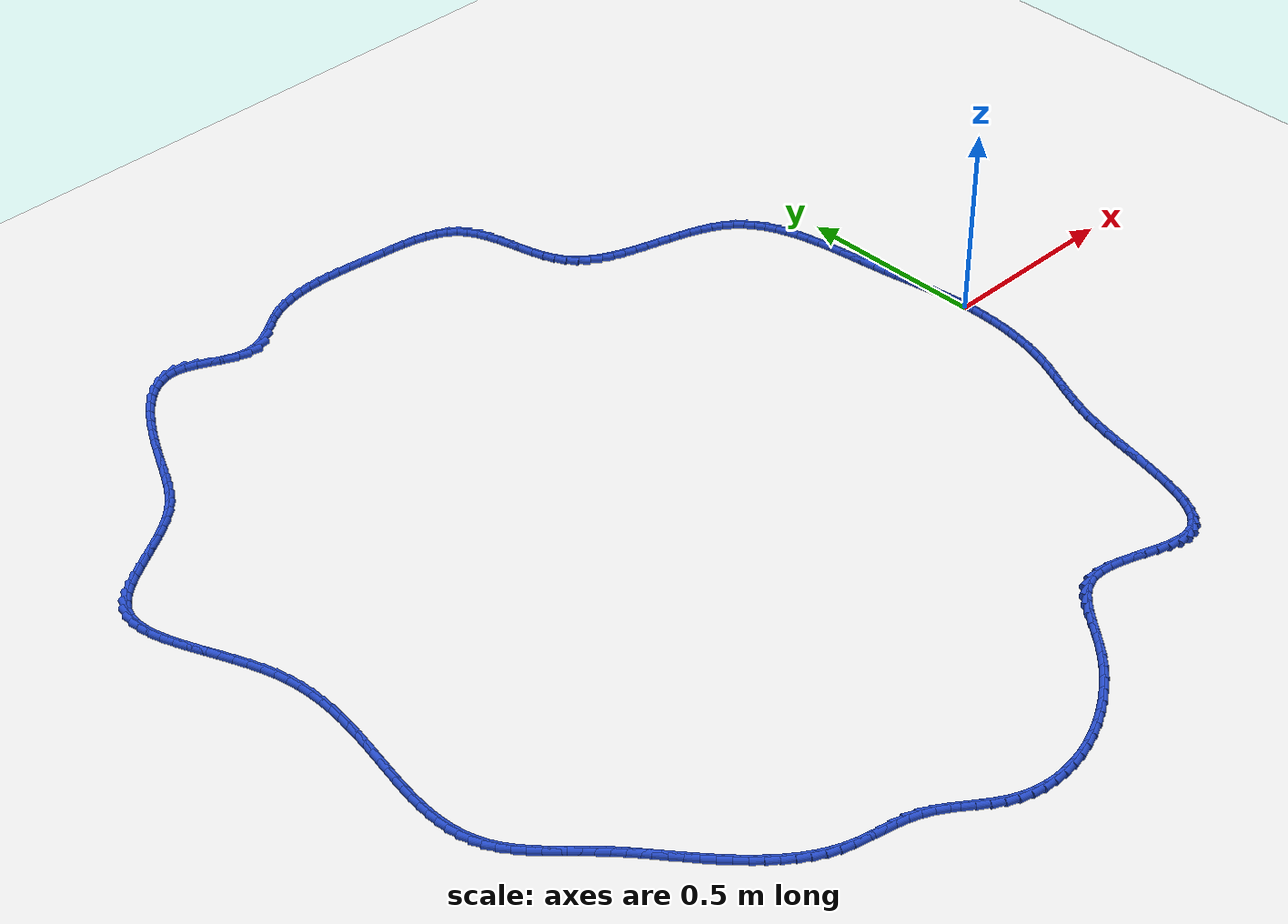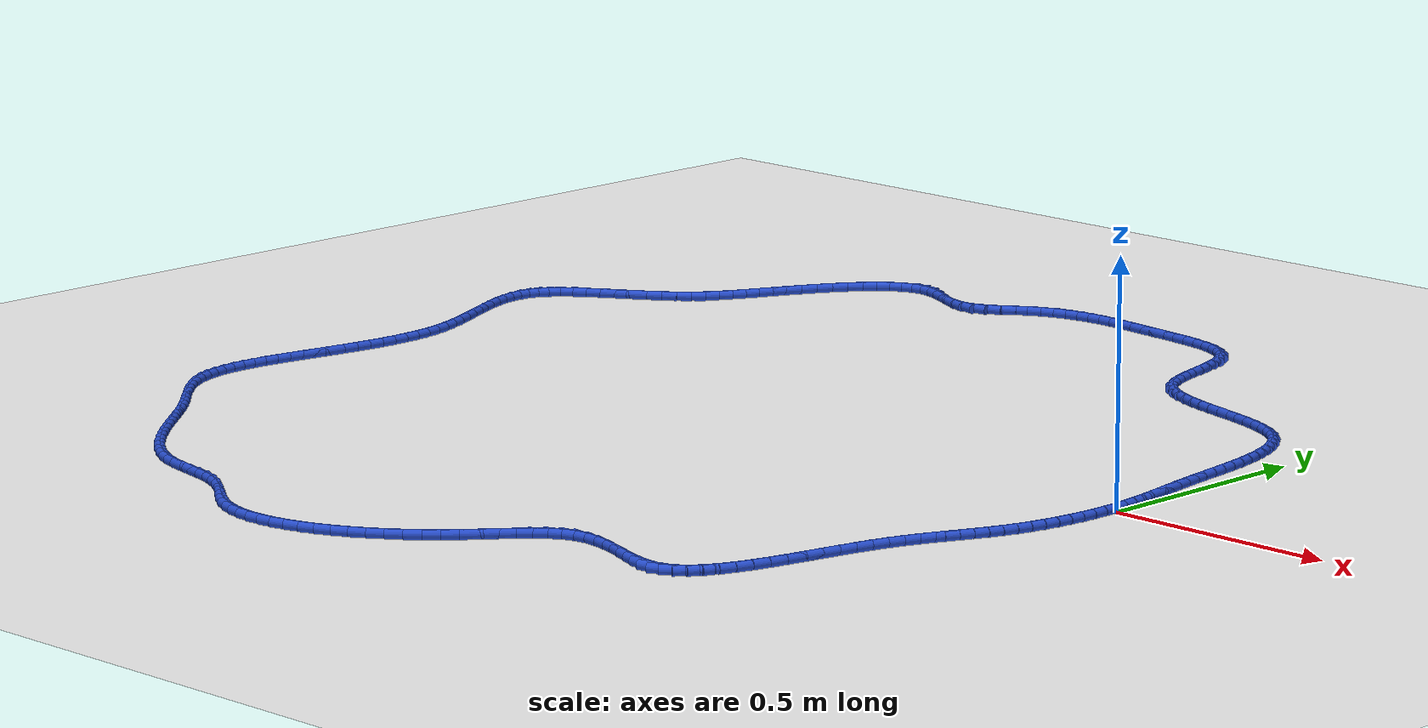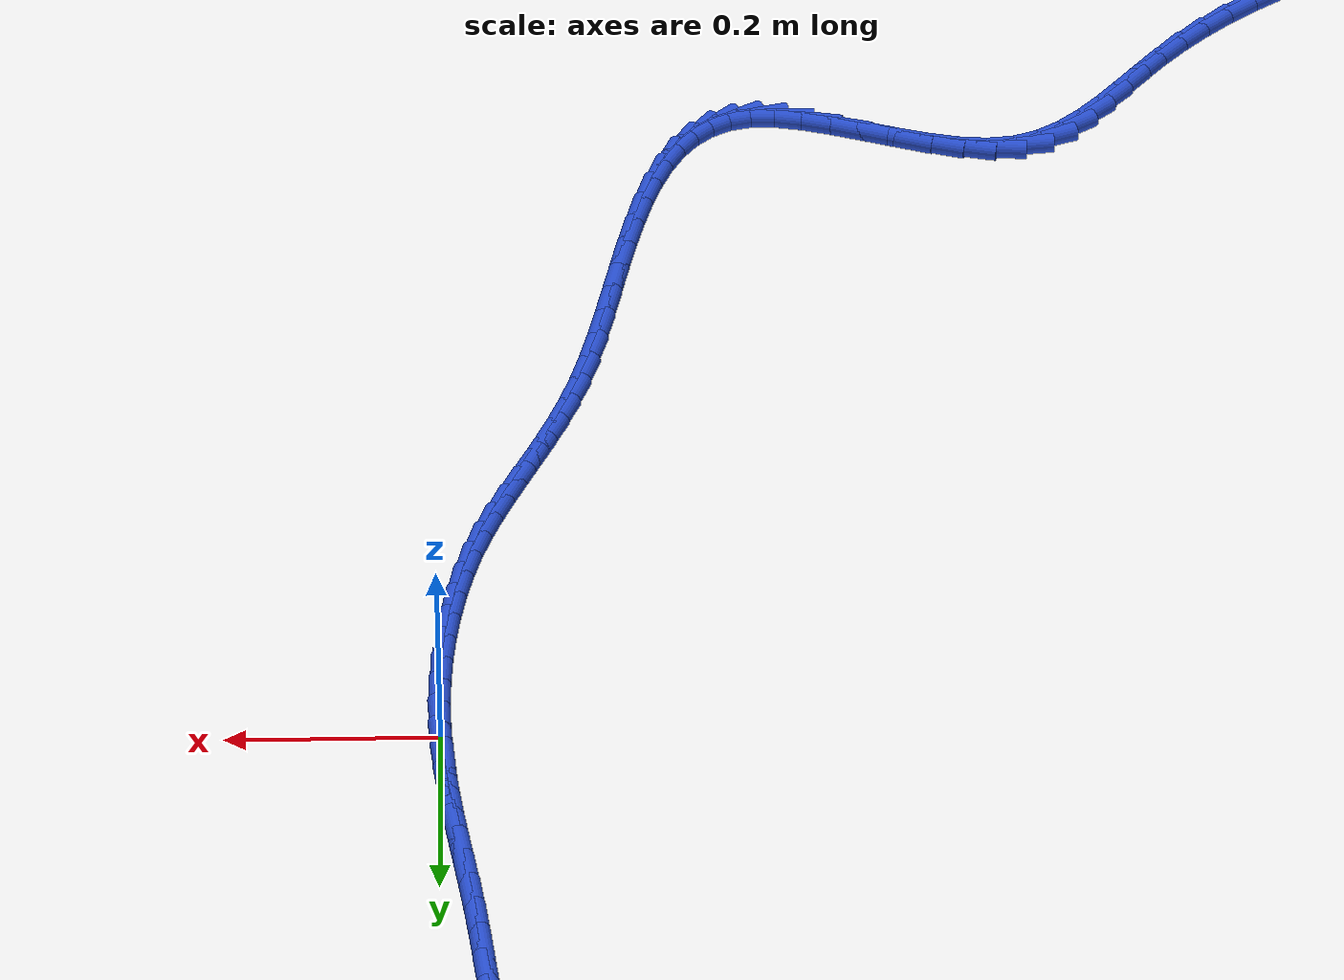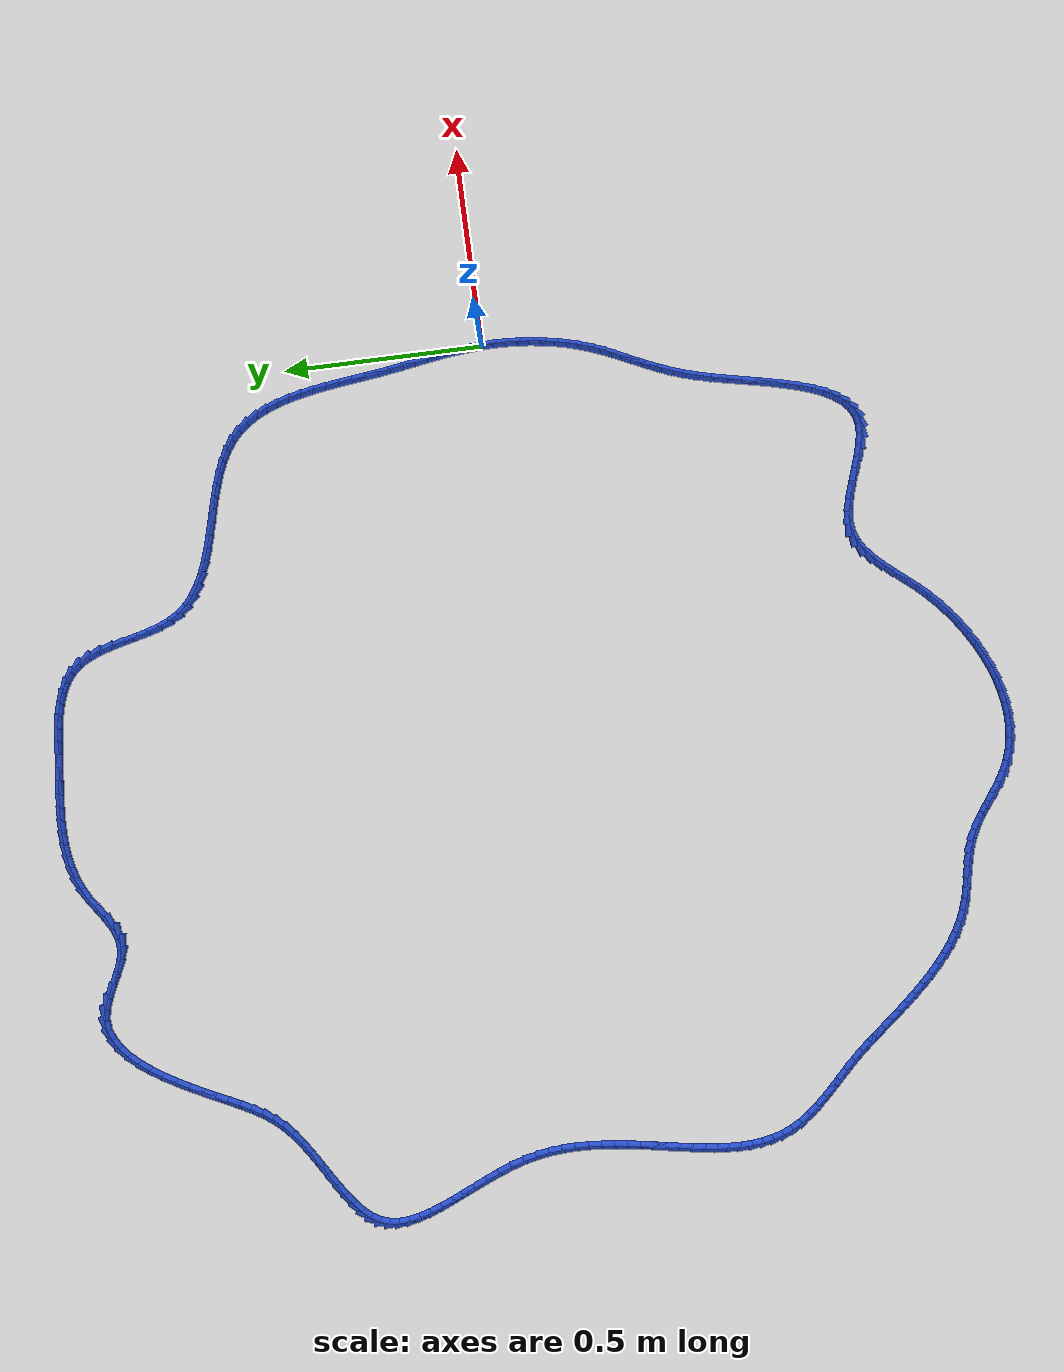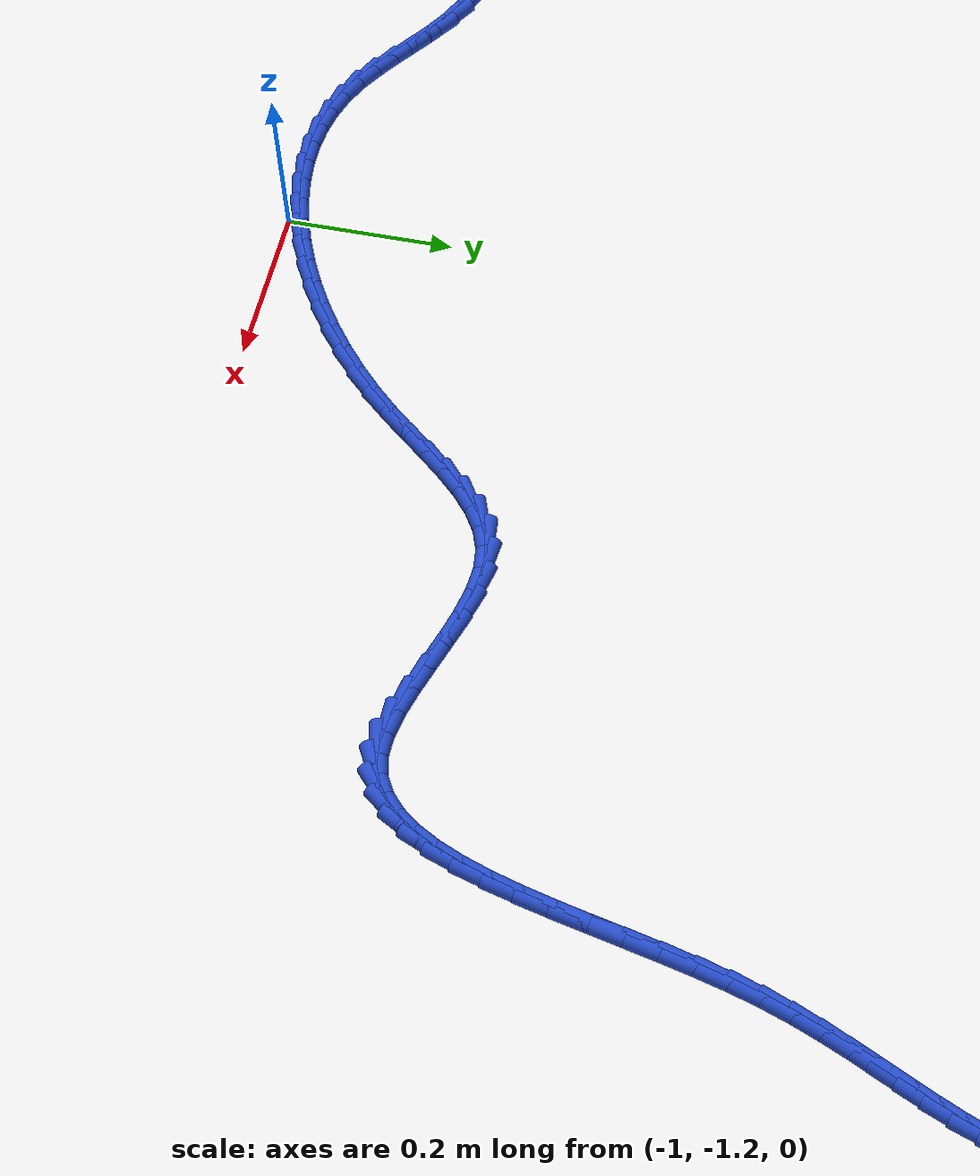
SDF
<sdf version="1.6">
 <world name="default">
  <light name="sun" type="directional">
   <pose>0 0 10 0 -0 0</pose>
   <diffuse>0.8 0.8 0.8 1</diffuse>
   <specular>0.2 0.2 0.2 1</specular>
   <attenuation>
    <range>1000</range>
    <constant>0.9</constant>
    <linear>0.01</linear>
    <quadratic>0.001</quadratic>
   </attenuation>
   <direction>-0.5 0.1 -0.9</direction>
  </light>
  <model name="ground_plane">
   <static>1</static>
   <link name="link">
    <collision name="collision">
     <geometry><plane><normal>0 0 1</normal><size>100 100</size></plane></geometry>
     <surface><friction><ode><mu>100</mu><mu2>50</mu2></ode></friction></surface>
    </collision>
    <visual name="visual">
     <cast_shadows>0</cast_shadows>
     <geometry><plane><normal>0 0 1</normal><size>100 100</size></plane></geometry>
     <material>
      <script><uri>file://media/materials/scripts/gazebo.material</uri><name>Gazebo/WhiteGlow</name></script>
     </material>
    </visual>
   </link>
  </model>
  <gravity>0 0 -9.8</gravity>
  <magnetic_field>6e-06 2.3e-05 -4.2e-05</magnetic_field>
  <atmosphere type="adiabatic"/>
  <physics name="default_physics" default="0" type="ode">
   <max_step_size>0.001</max_step_size>
   <real_time_factor>1</real_time_factor>
   <real_time_update_rate>1000</real_time_update_rate>
  </physics>
  <scene><ambient>0.4 0.4 0.4 1</ambient><background>0.7 0.7 0.7 1</background><shadows>1</shadows></scene>
  <spherical_coordinates>
   <surface_model>EARTH_WGS84</surface_model>
   <latitude_deg>0</latitude_deg>
   <longitude_deg>0</longitude_deg>
   <elevation>0</elevation>
   <heading_deg>0</heading_deg>
  </spherical_coordinates>
  <model name="line">
   <link name="link_0">
    <pose>3.469446951953614e-18 6.938893903907228e-18 0.01 0 1.57 -1.5096084813208515</pose>
    <collision name="collision">
     <geometry><cylinder><radius>0.01</radius><length>0.08</length></cylinder></geometry>
    </collision>
    <visual name="visual">
     <material>
      <script><name>Gazebo/Blue</name><uri>file://media/materials/scripts/gazebo.material</uri></script>
     </material>
     <geometry><cylinder><radius>0.01</radius><length>0.08</length></cylinder></geometry>
    </visual>
   </link>
   <link name="link_1">
    <pose>-0.001852559912339359 0.03023880568668892 0.01 0 1.57 -1.4762304032931488</pose>
    <collision name="collision">
     <geometry><cylinder><radius>0.01</radius><length>0.08</length></cylinder></geometry>
    </collision>
    <visual name="visual">
     <material>
      <script><name>Gazebo/Blue</name><uri>file://media/materials/scripts/gazebo.material</uri></script>
     </material>
     <geometry><cylinder><radius>0.01</radius><length>0.08</length></cylinder></geometry>
    </visual>
   </link>
   <link name="link_2">
    <pose>-0.0046914120962163125 0.06016908799199582 0.01 0 1.57 -1.4493752729071308</pose>
    <collision name="collision">
     <geometry><cylinder><radius>0.01</radius><length>0.08</length></cylinder></geometry>
    </collision>
    <visual name="visual">
     <material>
      <script><name>Gazebo/Blue</name><uri>file://media/materials/scripts/gazebo.material</uri></script>
     </material>
     <geometry><cylinder><radius>0.01</radius><length>0.08</length></cylinder></geometry>
    </visual>
   </link>
   <link name="link_3">
    <pose>-0.008323980284288846 0.08993903943934645 0.01 0 1.57 -1.4294726162318496</pose>
    <collision name="collision">
     <geometry><cylinder><radius>0.01</radius><length>0.08</length></cylinder></geometry>
    </collision>
    <visual name="visual">
     <material>
      <script><name>Gazebo/Blue</name><uri>file://media/materials/scripts/gazebo.material</uri></script>
     </material>
     <geometry><cylinder><radius>0.01</radius><length>0.08</length></cylinder></geometry>
    </visual>
   </link>
   <link name="link_4">
    <pose>-0.012557688209214954 0.11969685255216661 0.01 0 1.57 -1.4167351201665477</pose>
    <collision name="collision">
     <geometry><cylinder><radius>0.01</radius><length>0.08</length></cylinder></geometry>
    </collision>
    <visual name="visual">
     <material>
      <script><name>Gazebo/Blue</name><uri>file://media/materials/scripts/gazebo.material</uri></script>
     </material>
     <geometry><cylinder><radius>0.01</radius><length>0.08</length></cylinder></geometry>
    </visual>
   </link>
   <link name="link_5">
    <pose>-0.017199959603652618 0.14959071985388206 0.01 0 1.57 -1.411179671405073</pose>
    <collision name="collision">
     <geometry><cylinder><radius>0.01</radius><length>0.08</length></cylinder></geometry>
    </collision>
    <visual name="visual">
     <material>
      <script><name>Gazebo/Blue</name><uri>file://media/materials/scripts/gazebo.material</uri></script>
     </material>
     <geometry><cylinder><radius>0.01</radius><length>0.08</length></cylinder></geometry>
    </visual>
   </link>
   <link name="link_6">
    <pose>-0.022058218200259827 0.17976883386791856 0.01 0 1.57 -1.4126513596155346</pose>
    <collision name="collision">
     <geometry><cylinder><radius>0.01</radius><length>0.08</length></cylinder></geometry>
    </collision>
    <visual name="visual">
     <material>
      <script><name>Gazebo/Blue</name><uri>file://media/materials/scripts/gazebo.material</uri></script>
     </material>
     <geometry><cylinder><radius>0.01</radius><length>0.08</length></cylinder></geometry>
    </visual>
   </link>
   <link name="link_7">
    <pose>-0.026939887731694565 0.21037938711770188 0.01 0 1.57 -1.420845924906378</pose>
    <collision name="collision">
     <geometry><cylinder><radius>0.01</radius><length>0.08</length></cylinder></geometry>
    </collision>
    <visual name="visual">
     <material>
      <script><name>Gazebo/Blue</name><uri>file://media/materials/scripts/gazebo.material</uri></script>
     </material>
     <geometry><cylinder><radius>0.01</radius><length>0.08</length></cylinder></geometry>
    </visual>
   </link>
   <link name="link_8">
    <pose>-0.03165239193061482 0.2415705721266577 0.01 0 1.57 -1.4350782630489296</pose>
    <collision name="collision">
     <geometry><cylinder><radius>0.01</radius><length>0.08</length></cylinder></geometry>
    </collision>
    <visual name="visual">
     <material>
      <script><name>Gazebo/Blue</name><uri>file://media/materials/scripts/gazebo.material</uri></script>
     </material>
     <geometry><cylinder><radius>0.01</radius><length>0.08</length></cylinder></geometry>
    </visual>
   </link>
   <link name="link_9">
    <pose>-0.036010395214238156 0.27348388558959497 0.01 0 1.57 -1.4479194386062304</pose>
    <collision name="collision">
     <geometry><cylinder><radius>0.01</radius><length>0.08</length></cylinder></geometry>
    </collision>
    <visual name="visual">
     <material>
      <script><name>Gazebo/Blue</name><uri>file://media/materials/scripts/gazebo.material</uri></script>
     </material>
     <geometry><cylinder><radius>0.01</radius><length>0.08</length></cylinder></geometry>
    </visual>
   </link>
   <link name="link_10">
    <pose>-0.040034766978417895 0.3060701359886892 0.01 0 1.57 -1.4518741688276657</pose>
    <collision name="collision">
     <geometry><cylinder><radius>0.01</radius><length>0.08</length></cylinder></geometry>
    </collision>
    <visual name="visual">
     <material>
      <script><name>Gazebo/Blue</name><uri>file://media/materials/scripts/gazebo.material</uri></script>
     </material>
     <geometry><cylinder><radius>0.01</radius><length>0.08</length></cylinder></geometry>
    </visual>
   </link>
   <link name="link_11">
    <pose>-0.043977371662708334 0.3390665189617418 0.01 0 1.57 -1.446935587223106</pose>
    <collision name="collision">
     <geometry><cylinder><radius>0.01</radius><length>0.08</length></cylinder></geometry>
    </collision>
    <visual name="visual">
     <material>
      <script><name>Gazebo/Blue</name><uri>file://media/materials/scripts/gazebo.material</uri></script>
     </material>
     <geometry><cylinder><radius>0.01</radius><length>0.08</length></cylinder></geometry>
    </visual>
   </link>
   <link name="link_12">
    <pose>-0.04810229244388441 0.3721989308599093 0.01 0 1.57 -1.4331241427845258</pose>
    <collision name="collision">
     <geometry><cylinder><radius>0.01</radius><length>0.08</length></cylinder></geometry>
    </collision>
    <visual name="visual">
     <material>
      <script><name>Gazebo/Blue</name><uri>file://media/materials/scripts/gazebo.material</uri></script>
     </material>
     <geometry><cylinder><radius>0.01</radius><length>0.08</length></cylinder></geometry>
    </visual>
   </link>
   <link name="link_13">
    <pose>-0.05267361249872108 0.4051932680343479 0.01 0 1.57 -1.4100871413520688</pose>
    <collision name="collision">
     <geometry><cylinder><radius>0.01</radius><length>0.08</length></cylinder></geometry>
    </collision>
    <visual name="visual">
     <material>
      <script><name>Gazebo/Blue</name><uri>file://media/materials/scripts/gazebo.material</uri></script>
     </material>
     <geometry><cylinder><radius>0.01</radius><length>0.08</length></cylinder></geometry>
    </visual>
   </link>
   <link name="link_14">
    <pose>-0.05795541500399326 0.43777542683621395 0.01 0 1.57 -1.3771056604337633</pose>
    <collision name="collision">
     <geometry><cylinder><radius>0.01</radius><length>0.08</length></cylinder></geometry>
    </collision>
    <visual name="visual">
     <material>
      <script><name>Gazebo/Blue</name><uri>file://media/materials/scripts/gazebo.material</uri></script>
     </material>
     <geometry><cylinder><radius>0.01</radius><length>0.08</length></cylinder></geometry>
    </visual>
   </link>
   <link name="link_15">
    <pose>-0.06421178313647594 0.4696713036166642 0.01 0 1.57 -1.3330976732777582</pose>
    <collision name="collision">
     <geometry><cylinder><radius>0.01</radius><length>0.08</length></cylinder></geometry>
    </collision>
    <visual name="visual">
     <material>
      <script><name>Gazebo/Blue</name><uri>file://media/materials/scripts/gazebo.material</uri></script>
     </material>
     <geometry><cylinder><radius>0.01</radius><length>0.08</length></cylinder></geometry>
    </visual>
   </link>
   <link name="link_16">
    <pose>-0.07170680007294399 0.5006067947268548 0.01 0 1.57 -1.2766405419950497</pose>
    <collision name="collision">
     <geometry><cylinder><radius>0.01</radius><length>0.08</length></cylinder></geometry>
    </collision>
    <visual name="visual">
     <material>
      <script><name>Gazebo/Blue</name><uri>file://media/materials/scripts/gazebo.material</uri></script>
     </material>
     <geometry><cylinder><radius>0.01</radius><length>0.08</length></cylinder></geometry>
    </visual>
   </link>
   <link name="link_17">
    <pose>-0.0807045489901724 0.5303077965179422 0.01 0 1.57 -1.2060556369249278</pose>
    <collision name="collision">
     <geometry><cylinder><radius>0.01</radius><length>0.08</length></cylinder></geometry>
    </collision>
    <visual name="visual">
     <material>
      <script><name>Gazebo/Blue</name><uri>file://media/materials/scripts/gazebo.material</uri></script>
     </material>
     <geometry><cylinder><radius>0.01</radius><length>0.08</length></cylinder></geometry>
    </visual>
   </link>
   <link name="link_18">
    <pose>-0.0914691130649361 0.558500205341083 0.01 0 1.57 -1.119626753373811</pose>
    <collision name="collision">
     <geometry><cylinder><radius>0.01</radius><length>0.08</length></cylinder></geometry>
    </collision>
    <visual name="visual">
     <material>
      <script><name>Gazebo/Blue</name><uri>file://media/materials/scripts/gazebo.material</uri></script>
     </material>
     <geometry><cylinder><radius>0.01</radius><length>0.08</length></cylinder></geometry>
    </visual>
   </link>
   <link name="link_19">
    <pose>-0.10426457547401001 0.5849099175474333 0.01 0 1.57 -1.0160486485261653</pose>
    <collision name="collision">
     <geometry><cylinder><radius>0.01</radius><length>0.08</length></cylinder></geometry>
    </collision>
    <visual name="visual">
     <material>
      <script><name>Gazebo/Blue</name><uri>file://media/materials/scripts/gazebo.material</uri></script>
     </material>
     <geometry><cylinder><radius>0.01</radius><length>0.08</length></cylinder></geometry>
    </visual>
   </link>
   <link name="link_20">
    <pose>-0.11935501939416912 0.6092628294881497 0.01 0 1.57 -0.8951726852559022</pose>
    <collision name="collision">
     <geometry><cylinder><radius>0.01</radius><length>0.08</length></cylinder></geometry>
    </collision>
    <visual name="visual">
     <material>
      <script><name>Gazebo/Blue</name><uri>file://media/materials/scripts/gazebo.material</uri></script>
     </material>
     <geometry><cylinder><radius>0.01</radius><length>0.08</length></cylinder></geometry>
    </visual>
   </link>
   <link name="link_21">
    <pose>-0.1370045280021883 0.6312848375143887 0.01 0 1.57 -0.7589405687826736</pose>
    <collision name="collision">
     <geometry><cylinder><radius>0.01</radius><length>0.08</length></cylinder></geometry>
    </collision>
    <visual name="visual">
     <material>
      <script><name>Gazebo/Blue</name><uri>file://media/materials/scripts/gazebo.material</uri></script>
     </material>
     <geometry><cylinder><radius>0.01</radius><length>0.08</length></cylinder></geometry>
    </visual>
   </link>
   <link name="link_22">
    <pose>-0.15747717167615702 0.65070185049639 0.01 0 1.57 -0.6186227134365173</pose>
    <collision name="collision">
     <geometry><cylinder><radius>0.01</radius><length>0.08</length></cylinder></geometry>
    </collision>
    <visual name="visual">
     <material>
      <script><name>Gazebo/Blue</name><uri>file://media/materials/scripts/gazebo.material</uri></script>
     </material>
     <geometry><cylinder><radius>0.01</radius><length>0.08</length></cylinder></geometry>
    </visual>
   </link>
   <link name="link_23">
    <pose>-0.18089931364129738 0.6673744760878453 0.01 0 1.57 -0.501227249246571</pose>
    <collision name="collision">
     <geometry><cylinder><radius>0.01</radius><length>0.08</length></cylinder></geometry>
    </collision>
    <visual name="visual">
     <material>
      <script><name>Gazebo/Blue</name><uri>file://media/materials/scripts/gazebo.material</uri></script>
     </material>
     <geometry><cylinder><radius>0.01</radius><length>0.08</length></cylinder></geometry>
    </visual>
   </link>
   <link name="link_24">
    <pose>-0.2069193954601897 0.6816308028626623 0.01 0 1.57 -0.4108660897879239</pose>
    <collision name="collision">
     <geometry><cylinder><radius>0.01</radius><length>0.08</length></cylinder></geometry>
    </collision>
    <visual name="visual">
     <material>
      <script><name>Gazebo/Blue</name><uri>file://media/materials/scripts/gazebo.material</uri></script>
     </material>
     <geometry><cylinder><radius>0.01</radius><length>0.08</length></cylinder></geometry>
    </visual>
   </link>
   <link name="link_25">
    <pose>-0.23508224733027594 0.6939002672517421 0.01 0 1.57 -0.34454319343561757</pose>
    <collision name="collision">
     <geometry><cylinder><radius>0.01</radius><length>0.08</length></cylinder></geometry>
    </collision>
    <visual name="visual">
     <material>
      <script><name>Gazebo/Blue</name><uri>file://media/materials/scripts/gazebo.material</uri></script>
     </material>
     <geometry><cylinder><radius>0.01</radius><length>0.08</length></cylinder></geometry>
    </visual>
   </link>
   <link name="link_26">
    <pose>-0.2649326994489988 0.704612305685987 0.01 0 1.57 -0.29908911575729025</pose>
    <collision name="collision">
     <geometry><cylinder><radius>0.01</radius><length>0.08</length></cylinder></geometry>
    </collision>
    <visual name="visual">
     <material>
      <script><name>Gazebo/Blue</name><uri>file://media/materials/scripts/gazebo.material</uri></script>
     </material>
     <geometry><cylinder><radius>0.01</radius><length>0.08</length></cylinder></geometry>
    </visual>
   </link>
   <link name="link_27">
    <pose>-0.29601558201380035 0.7141963545962977 0.01 0 1.57 -0.2719797004035659</pose>
    <collision name="collision">
     <geometry><cylinder><radius>0.01</radius><length>0.08</length></cylinder></geometry>
    </collision>
    <visual name="visual">
     <material>
      <script><name>Gazebo/Blue</name><uri>file://media/materials/scripts/gazebo.material</uri></script>
     </material>
     <geometry><cylinder><radius>0.01</radius><length>0.08</length></cylinder></geometry>
    </visual>
   </link>
   <link name="link_28">
    <pose>-0.32787572522212294 0.7230818504135762 0.01 0 1.57 -0.26160152540919646</pose>
    <collision name="collision">
     <geometry><cylinder><radius>0.01</radius><length>0.08</length></cylinder></geometry>
    </collision>
    <visual name="visual">
     <material>
      <script><name>Gazebo/Blue</name><uri>file://media/materials/scripts/gazebo.material</uri></script>
     </material>
     <geometry><cylinder><radius>0.01</radius><length>0.08</length></cylinder></geometry>
    </visual>
   </link>
   <link name="link_29">
    <pose>-0.36005795927140893 0.7316982295687235 0.01 0 1.57 -0.2672978482801051</pose>
    <collision name="collision">
     <geometry><cylinder><radius>0.01</radius><length>0.08</length></cylinder></geometry>
    </collision>
    <visual name="visual">
     <material>
      <script><name>Gazebo/Blue</name><uri>file://media/materials/scripts/gazebo.material</uri></script>
     </material>
     <geometry><cylinder><radius>0.01</radius><length>0.08</length></cylinder></geometry>
    </visual>
   </link>
   <link name="link_30">
    <pose>-0.3921071143591007 0.7404749284926415 0.01 0 1.57 -0.28936123270137243</pose>
    <collision name="collision">
     <geometry><cylinder><radius>0.01</radius><length>0.08</length></cylinder></geometry>
    </collision>
    <visual name="visual">
     <material>
      <script><name>Gazebo/Blue</name><uri>file://media/materials/scripts/gazebo.material</uri></script>
     </material>
     <geometry><cylinder><radius>0.01</radius><length>0.08</length></cylinder></geometry>
    </visual>
   </link>
   <link name="link_31">
    <pose>-0.4235680206826404 0.7498413836162315 0.01 0 1.57 -0.3290258023512551</pose>
    <collision name="collision">
     <geometry><cylinder><radius>0.01</radius><length>0.08</length></cylinder></geometry>
    </collision>
    <visual name="visual">
     <material>
      <script><name>Gazebo/Blue</name><uri>file://media/materials/scripts/gazebo.material</uri></script>
     </material>
     <geometry><cylinder><radius>0.01</radius><length>0.08</length></cylinder></geometry>
    </visual>
   </link>
   <link name="link_32">
    <pose>-0.4539855084394705 0.7602270313703948 0.01 0 1.57 -0.3884318092051939</pose>
    <collision name="collision">
     <geometry><cylinder><radius>0.01</radius><length>0.08</length></cylinder></geometry>
    </collision>
    <visual name="visual">
     <material>
      <script><name>Gazebo/Blue</name><uri>file://media/materials/scripts/gazebo.material</uri></script>
     </material>
     <geometry><cylinder><radius>0.01</radius><length>0.08</length></cylinder></geometry>
    </visual>
   </link>
   <link name="link_33">
    <pose>-0.48290440782703314 0.7720613081860329 0.01 0 1.57 -0.47044120005805695</pose>
    <collision name="collision">
     <geometry><cylinder><radius>0.01</radius><length>0.08</length></cylinder></geometry>
    </collision>
    <visual name="visual">
     <material>
      <script><name>Gazebo/Blue</name><uri>file://media/materials/scripts/gazebo.material</uri></script>
     </material>
     <geometry><cylinder><radius>0.01</radius><length>0.08</length></cylinder></geometry>
    </visual>
   </link>
   <link name="link_34">
    <pose>-0.5098695490427707 0.7857736504940473 0.01 0 1.57 -0.5780425654867221</pose>
    <collision name="collision">
     <geometry><cylinder><radius>0.01</radius><length>0.08</length></cylinder></geometry>
    </collision>
    <visual name="visual">
     <material>
      <script><name>Gazebo/Blue</name><uri>file://media/materials/scripts/gazebo.material</uri></script>
     </material>
     <geometry><cylinder><radius>0.01</radius><length>0.08</length></cylinder></geometry>
    </visual>
   </link>
   <link name="link_35">
    <pose>-0.5344257622841256 0.8017934947253396 0.01 0 1.57 -0.7129562302424629</pose>
    <collision name="collision">
     <geometry><cylinder><radius>0.01</radius><length>0.08</length></cylinder></geometry>
    </collision>
    <visual name="visual">
     <material>
      <script><name>Gazebo/Blue</name><uri>file://media/materials/scripts/gazebo.material</uri></script>
     </material>
     <geometry><cylinder><radius>0.01</radius><length>0.08</length></cylinder></geometry>
    </visual>
   </link>
   <link name="link_36">
    <pose>-0.55611787774854 0.8205502773108111 0.01 0 1.57 -0.873276985239991</pose>
    <collision name="collision">
     <geometry><cylinder><radius>0.01</radius><length>0.08</length></cylinder></geometry>
    </collision>
    <visual name="visual">
     <material>
      <script><name>Gazebo/Blue</name><uri>file://media/materials/scripts/gazebo.material</uri></script>
     </material>
     <geometry><cylinder><radius>0.01</radius><length>0.08</length></cylinder></geometry>
    </visual>
   </link>
   <link name="link_37">
    <pose>-0.5744907256334563 0.8424734346813634 0.01 0 1.57 -1.0436542021579869</pose>
    <collision name="collision">
     <geometry><cylinder><radius>0.01</radius><length>0.08</length></cylinder></geometry>
    </collision>
    <visual name="visual">
     <material>
      <script><name>Gazebo/Blue</name><uri>file://media/materials/scripts/gazebo.material</uri></script>
     </material>
     <geometry><cylinder><radius>0.01</radius><length>0.08</length></cylinder></geometry>
    </visual>
   </link>
   <link name="link_38">
    <pose>-0.5892523367080302 0.8678333482559238 0.01 0 1.57 -1.1774554467372966</pose>
    <collision name="collision">
     <geometry><cylinder><radius>0.01</radius><length>0.08</length></cylinder></geometry>
    </collision>
    <visual name="visual">
     <material>
      <script><name>Gazebo/Blue</name><uri>file://media/materials/scripts/gazebo.material</uri></script>
     </material>
     <geometry><cylinder><radius>0.01</radius><length>0.08</length></cylinder></geometry>
    </visual>
   </link>
   <link name="link_39">
    <pose>-0.6009676216913108 0.8960652856467695 0.01 0 1.57 -1.2662276992774717</pose>
    <collision name="collision">
     <geometry><cylinder><radius>0.01</radius><length>0.08</length></cylinder></geometry>
    </collision>
    <visual name="visual">
     <material>
      <script><name>Gazebo/Blue</name><uri>file://media/materials/scripts/gazebo.material</uri></script>
     </material>
     <geometry><cylinder><radius>0.01</radius><length>0.08</length></cylinder></geometry>
    </visual>
   </link>
   <link name="link_40">
    <pose>-0.6104817434908949 0.9263313811386586 0.01 0 1.57 -1.3170803648951959</pose>
    <collision name="collision">
     <geometry><cylinder><radius>0.01</radius><length>0.08</length></cylinder></geometry>
    </collision>
    <visual name="visual">
     <material>
      <script><name>Gazebo/Blue</name><uri>file://media/materials/scripts/gazebo.material</uri></script>
     </material>
     <geometry><cylinder><radius>0.01</radius><length>0.08</length></cylinder></geometry>
    </visual>
   </link>
   <link name="link_41">
    <pose>-0.6186400243481444 0.95779361372992 0.01 0 1.57 -1.3349281189691748</pose>
    <collision name="collision">
     <geometry><cylinder><radius>0.01</radius><length>0.08</length></cylinder></geometry>
    </collision>
    <visual name="visual">
     <material>
      <script><name>Gazebo/Blue</name><uri>file://media/materials/scripts/gazebo.material</uri></script>
     </material>
     <geometry><cylinder><radius>0.01</radius><length>0.08</length></cylinder></geometry>
    </visual>
   </link>
   <link name="link_42">
    <pose>-0.6262877865044214 0.9896139624188824 0.01 0 1.57 -1.3213944151721413</pose>
    <collision name="collision">
     <geometry><cylinder><radius>0.01</radius><length>0.08</length></cylinder></geometry>
    </collision>
    <visual name="visual">
     <material>
      <script><name>Gazebo/Blue</name><uri>file://media/materials/scripts/gazebo.material</uri></script>
     </material>
     <geometry><cylinder><radius>0.01</radius><length>0.08</length></cylinder></geometry>
    </visual>
   </link>
   <link name="link_43">
    <pose>-0.6342703522010881 1.020954406203875 0.01 0 1.57 -1.2745812585451735</pose>
    <collision name="collision">
     <geometry><cylinder><radius>0.01</radius><length>0.08</length></cylinder></geometry>
    </collision>
    <visual name="visual">
     <material>
      <script><name>Gazebo/Blue</name><uri>file://media/materials/scripts/gazebo.material</uri></script>
     </material>
     <geometry><cylinder><radius>0.01</radius><length>0.08</length></cylinder></geometry>
    </visual>
   </link>
   <link name="link_44">
    <pose>-0.6434330436795066 1.0509769240832258 0.01 0 1.57 -1.1890064386980166</pose>
    <collision name="collision">
     <geometry><cylinder><radius>0.01</radius><length>0.08</length></cylinder></geometry>
    </collision>
    <visual name="visual">
     <material>
      <script><name>Gazebo/Blue</name><uri>file://media/materials/scripts/gazebo.material</uri></script>
     </material>
     <geometry><cylinder><radius>0.01</radius><length>0.08</length></cylinder></geometry>
    </visual>
   </link>
   <link name="link_45">
    <pose>-0.6546211831810391 1.0788434950552643 0.01 0 1.57 -1.056330328687823</pose>
    <collision name="collision">
     <geometry><cylinder><radius>0.01</radius><length>0.08</length></cylinder></geometry>
    </collision>
    <visual name="visual">
     <material>
      <script><name>Gazebo/Blue</name><uri>file://media/materials/scripts/gazebo.material</uri></script>
     </material>
     <geometry><cylinder><radius>0.01</radius><length>0.08</length></cylinder></geometry>
    </visual>
   </link>
   <link name="link_46">
    <pose>-0.6686800929470476 1.103716098118319 0.01 0 1.57 -0.8696956677434259</pose>
    <collision name="collision">
     <geometry><cylinder><radius>0.01</radius><length>0.08</length></cylinder></geometry>
    </collision>
    <visual name="visual">
     <material>
      <script><name>Gazebo/Blue</name><uri>file://media/materials/scripts/gazebo.material</uri></script>
     </material>
     <geometry><cylinder><radius>0.01</radius><length>0.08</length></cylinder></geometry>
    </visual>
   </link>
   <link name="link_47">
    <pose>-0.686447901957074 1.1247637239685921 0.01 0 1.57 -0.6592602692911168</pose>
    <collision name="collision">
     <geometry><cylinder><radius>0.01</radius><length>0.08</length></cylinder></geometry>
    </collision>
    <visual name="visual">
     <material>
      <script><name>Gazebo/Blue</name><uri>file://media/materials/scripts/gazebo.material</uri></script>
     </material>
     <geometry><cylinder><radius>0.01</radius><length>0.08</length></cylinder></geometry>
    </visual>
   </link>
   <link name="link_48">
    <pose>-0.7082480272638756 1.1416570834693478 0.01 0 1.57 -0.4819672961127319</pose>
    <collision name="collision">
     <geometry><cylinder><radius>0.01</radius><length>0.08</length></cylinder></geometry>
    </collision>
    <visual name="visual">
     <material>
      <script><name>Gazebo/Blue</name><uri>file://media/materials/scripts/gazebo.material</uri></script>
     </material>
     <geometry><cylinder><radius>0.01</radius><length>0.08</length></cylinder></geometry>
    </visual>
   </link>
   <link name="link_49">
    <pose>-0.7335542214095824 1.1548951057512666 0.01 0 1.57 -0.34570527650419036</pose>
    <collision name="collision">
     <geometry><cylinder><radius>0.01</radius><length>0.08</length></cylinder></geometry>
    </collision>
    <visual name="visual">
     <material>
      <script><name>Gazebo/Blue</name><uri>file://media/materials/scripts/gazebo.material</uri></script>
     </material>
     <geometry><cylinder><radius>0.01</radius><length>0.08</length></cylinder></geometry>
    </visual>
   </link>
   <link name="link_50">
    <pose>-0.7617607310012315 1.1650542190837923 0.01 0 1.57 -0.24594625557700184</pose>
    <collision name="collision">
     <geometry><cylinder><radius>0.01</radius><length>0.08</length></cylinder></geometry>
    </collision>
    <visual name="visual">
     <material>
      <script><name>Gazebo/Blue</name><uri>file://media/materials/scripts/gazebo.material</uri></script>
     </material>
     <geometry><cylinder><radius>0.01</radius><length>0.08</length></cylinder></geometry>
    </visual>
   </link>
   <link name="link_51">
    <pose>-0.7922618026458601 1.1727108517363691 0.01 0 1.57 -0.17617856483725677</pose>
    <collision name="collision">
     <geometry><cylinder><radius>0.01</radius><length>0.08</length></cylinder></geometry>
    </collision>
    <visual name="visual">
     <material>
      <script><name>Gazebo/Blue</name><uri>file://media/materials/scripts/gazebo.material</uri></script>
     </material>
     <geometry><cylinder><radius>0.01</radius><length>0.08</length></cylinder></geometry>
    </visual>
   </link>
   <link name="link_52">
    <pose>-0.8244516829505055 1.1784414319784413 0.01 0 1.57 -0.1309142001120842</pose>
    <collision name="collision">
     <geometry><cylinder><radius>0.01</radius><length>0.08</length></cylinder></geometry>
    </collision>
    <visual name="visual">
     <material>
      <script><name>Gazebo/Blue</name><uri>file://media/materials/scripts/gazebo.material</uri></script>
     </material>
     <geometry><cylinder><radius>0.01</radius><length>0.08</length></cylinder></geometry>
    </visual>
   </link>
   <link name="link_53">
    <pose>-0.857724618522204 1.1828223880794526 0.01 0 1.57 -0.10649145984250988</pose>
    <collision name="collision">
     <geometry><cylinder><radius>0.01</radius><length>0.08</length></cylinder></geometry>
    </collision>
    <visual name="visual">
     <material>
      <script><name>Gazebo/Blue</name><uri>file://media/materials/scripts/gazebo.material</uri></script>
     </material>
     <geometry><cylinder><radius>0.01</radius><length>0.08</length></cylinder></geometry>
    </visual>
   </link>
   <link name="link_54">
    <pose>-0.891474855967994 1.186430148308848 0.01 0 1.57 -0.10093901053864456</pose>
    <collision name="collision">
     <geometry><cylinder><radius>0.01</radius><length>0.08</length></cylinder></geometry>
    </collision>
    <visual name="visual">
     <material>
      <script><name>Gazebo/Blue</name><uri>file://media/materials/scripts/gazebo.material</uri></script>
     </material>
     <geometry><cylinder><radius>0.01</radius><length>0.08</length></cylinder></geometry>
    </visual>
   </link>
   <link name="link_55">
    <pose>-0.925100107111866 1.1898358221973588 0.01 0 1.57 -0.10344419947631227</pose>
    <collision name="collision">
     <geometry><cylinder><radius>0.01</radius><length>0.08</length></cylinder></geometry>
    </collision>
    <visual name="visual">
     <material>
      <script><name>Gazebo/Blue</name><uri>file://media/materials/scripts/gazebo.material</uri></script>
     </material>
     <geometry><cylinder><radius>0.01</radius><length>0.08</length></cylinder></geometry>
    </visual>
   </link>
   <link name="link_56">
    <pose>-0.9582174037894959 1.193273886432345 0.01 0 1.57 -0.09710016064013774</pose>
    <collision name="collision">
     <geometry><cylinder><radius>0.01</radius><length>0.08</length></cylinder></geometry>
    </collision>
    <visual name="visual">
     <material>
      <script><name>Gazebo/Blue</name><uri>file://media/materials/scripts/gazebo.material</uri></script>
     </material>
     <geometry><cylinder><radius>0.01</radius><length>0.08</length></cylinder></geometry>
    </visual>
   </link>
   <link name="link_57">
    <pose>-0.990790450337918 1.1964467123590379 0.01 0 1.57 -0.07986437645621547</pose>
    <collision name="collision">
     <geometry><cylinder><radius>0.01</radius><length>0.08</length></cylinder></geometry>
    </collision>
    <visual name="visual">
     <material>
      <script><name>Gazebo/Blue</name><uri>file://media/materials/scripts/gazebo.material</uri></script>
     </material>
     <geometry><cylinder><radius>0.01</radius><length>0.08</length></cylinder></geometry>
    </visual>
   </link>
   <link name="link_58">
    <pose>-1.0228135726522698 1.1990096704945503 0.01 0 1.57 -0.05107050131117894</pose>
    <collision name="collision">
     <geometry><cylinder><radius>0.01</radius><length>0.08</length></cylinder></geometry>
    </collision>
    <visual name="visual">
     <material>
      <script><name>Gazebo/Blue</name><uri>file://media/materials/scripts/gazebo.material</uri></script>
     </material>
     <geometry><cylinder><radius>0.01</radius><length>0.08</length></cylinder></geometry>
    </visual>
   </link>
   <link name="link_59">
    <pose>-1.0542810966276874 1.2006181313559934 0.01 0 1.57 -0.010008453322910638</pose>
    <collision name="collision">
     <geometry><cylinder><radius>0.01</radius><length>0.08</length></cylinder></geometry>
    </collision>
    <visual name="visual">
     <material>
      <script><name>Gazebo/Blue</name><uri>file://media/materials/scripts/gazebo.material</uri></script>
     </material>
     <geometry><cylinder><radius>0.01</radius><length>0.08</length></cylinder></geometry>
    </visual>
   </link>
   <link name="link_60">
    <pose>-1.085187348159308 1.2009274654604796 0.01 0 1.57 0.04395495021374767</pose>
    <collision name="collision">
     <geometry><cylinder><radius>0.01</radius><length>0.08</length></cylinder></geometry>
    </collision>
    <visual name="visual">
     <material>
      <script><name>Gazebo/Blue</name><uri>file://media/materials/scripts/gazebo.material</uri></script>
     </material>
     <geometry><cylinder><radius>0.01</radius><length>0.08</length></cylinder></geometry>
    </visual>
   </link>
   <link name="link_61">
    <pose>-1.115526653142268 1.1995930433251212 0.01 0 1.57 0.11116818963260791</pose>
    <collision name="collision">
     <geometry><cylinder><radius>0.01</radius><length>0.08</length></cylinder></geometry>
    </collision>
    <visual name="visual">
     <material>
      <script><name>Gazebo/Blue</name><uri>file://media/materials/scripts/gazebo.material</uri></script>
     </material>
     <geometry><cylinder><radius>0.01</radius><length>0.08</length></cylinder></geometry>
    </visual>
   </link>
   <link name="link_62">
    <pose>-1.1452933374717043 1.1962702354670298 0.01 0 1.57 0.19139769231253775</pose>
    <collision name="collision">
     <geometry><cylinder><radius>0.01</radius><length>0.08</length></cylinder></geometry>
    </collision>
    <visual name="visual">
     <material>
      <script><name>Gazebo/Blue</name><uri>file://media/materials/scripts/gazebo.material</uri></script>
     </material>
     <geometry><cylinder><radius>0.01</radius><length>0.08</length></cylinder></geometry>
    </visual>
   </link>
   <link name="link_63">
    <pose>-1.1744817270427543 1.190614412403318 0.01 0 1.57 0.28348838075562377</pose>
    <collision name="collision">
     <geometry><cylinder><radius>0.01</radius><length>0.08</length></cylinder></geometry>
    </collision>
    <visual name="visual">
     <material>
      <script><name>Gazebo/Blue</name><uri>file://media/materials/scripts/gazebo.material</uri></script>
     </material>
     <geometry><cylinder><radius>0.01</radius><length>0.08</length></cylinder></geometry>
    </visual>
   </link>
   <link name="link_64">
    <pose>-1.2030861477505543 1.1822809446510976 0.01 0 1.57 0.3851084420166745</pose>
    <collision name="collision">
     <geometry><cylinder><radius>0.01</radius><length>0.08</length></cylinder></geometry>
    </collision>
    <visual name="visual">
     <material>
      <script><name>Gazebo/Blue</name><uri>file://media/materials/scripts/gazebo.material</uri></script>
     </material>
     <geometry><cylinder><radius>0.01</radius><length>0.08</length></cylinder></geometry>
    </visual>
   </link>
   <link name="link_65">
    <pose>-1.2311009254902405 1.1709252027274804 0.01 0 1.57 0.4927442939534274</pose>
    <collision name="collision">
     <geometry><cylinder><radius>0.01</radius><length>0.08</length></cylinder></geometry>
    </collision>
    <visual name="visual">
     <material>
      <script><name>Gazebo/Blue</name><uri>file://media/materials/scripts/gazebo.material</uri></script>
     </material>
     <geometry><cylinder><radius>0.01</radius><length>0.08</length></cylinder></geometry>
    </visual>
   </link>
   <link name="link_66">
    <pose>-1.2585204510875778 1.1562031555582493 0.01 0 1.57 0.5822959400865786</pose>
    <collision name="collision">
     <geometry><cylinder><radius>0.01</radius><length>0.08</length></cylinder></geometry>
    </collision>
    <visual name="visual">
     <material>
      <script><name>Gazebo/Blue</name><uri>file://media/materials/scripts/gazebo.material</uri></script>
     </material>
     <geometry><cylinder><radius>0.01</radius><length>0.08</length></cylinder></geometry>
    </visual>
   </link>
   <link name="link_67">
    <pose>-1.2854174481959855 1.1384926970784308 0.01 0 1.57 0.5986438175385088</pose>
    <collision name="collision">
     <geometry><cylinder><radius>0.01</radius><length>0.08</length></cylinder></geometry>
    </collision>
    <visual name="visual">
     <material>
      <script><name>Gazebo/Blue</name><uri>file://media/materials/scripts/gazebo.material</uri></script>
     </material>
     <geometry><cylinder><radius>0.01</radius><length>0.08</length></cylinder></geometry>
    </visual>
   </link>
   <link name="link_68">
    <pose>-1.312094992209717 1.1202946713016098 0.01 0 1.57 0.5325506302736825</pose>
    <collision name="collision">
     <geometry><cylinder><radius>0.01</radius><length>0.08</length></cylinder></geometry>
    </collision>
    <visual name="visual">
     <material>
      <script><name>Gazebo/Blue</name><uri>file://media/materials/scripts/gazebo.material</uri></script>
     </material>
     <geometry><cylinder><radius>0.01</radius><length>0.08</length></cylinder></geometry>
    </visual>
   </link>
   <link name="link_69">
    <pose>-1.3388982878914208 1.1044981917010415 0.01 0 1.57 0.3676759257074685</pose>
    <collision name="collision">
     <geometry><cylinder><radius>0.01</radius><length>0.08</length></cylinder></geometry>
    </collision>
    <visual name="visual">
     <material>
      <script><name>Gazebo/Blue</name><uri>file://media/materials/scripts/gazebo.material</uri></script>
     </material>
     <geometry><cylinder><radius>0.01</radius><length>0.08</length></cylinder></geometry>
    </visual>
   </link>
   <link name="link_70">
    <pose>-1.3661725400037468 1.0939923717499827 0.01 0 1.57 0.08561810151876548</pose>
    <collision name="collision">
     <geometry><cylinder><radius>0.01</radius><length>0.08</length></cylinder></geometry>
    </collision>
    <visual name="visual">
     <material>
      <script><name>Gazebo/Blue</name><uri>file://media/materials/scripts/gazebo.material</uri></script>
     </material>
     <geometry><cylinder><radius>0.01</radius><length>0.08</length></cylinder></geometry>
    </visual>
   </link>
   <link name="link_71">
    <pose>-1.3942524718715372 1.0915823295072533 0.01 0 1.57 -0.20186537929559234</pose>
    <collision name="collision">
     <geometry><cylinder><radius>0.01</radius><length>0.08</length></cylinder></geometry>
    </collision>
    <visual name="visual">
     <material>
      <script><name>Gazebo/Blue</name><uri>file://media/materials/scripts/gazebo.material</uri></script>
     </material>
     <geometry><cylinder><radius>0.01</radius><length>0.08</length></cylinder></geometry>
    </visual>
   </link>
   <link name="link_72">
    <pose>-1.4231512797092571 1.0974965515244197 0.01 0 1.57 -0.3725081465373291</pose>
    <collision name="collision">
     <geometry><cylinder><radius>0.01</radius><length>0.08</length></cylinder></geometry>
    </collision>
    <visual name="visual">
     <material>
      <script><name>Gazebo/Blue</name><uri>file://media/materials/scripts/gazebo.material</uri></script>
     </material>
     <geometry><cylinder><radius>0.01</radius><length>0.08</length></cylinder></geometry>
    </visual>
   </link>
   <link name="link_73">
    <pose>-1.4525083441110025 1.1089678668353984 0.01 0 1.57 -0.4465439583156662</pose>
    <collision name="collision">
     <geometry><cylinder><radius>0.01</radius><length>0.08</length></cylinder></geometry>
    </collision>
    <visual name="visual">
     <material>
      <script><name>Gazebo/Blue</name><uri>file://media/materials/scripts/gazebo.material</uri></script>
     </material>
     <geometry><cylinder><radius>0.01</radius><length>0.08</length></cylinder></geometry>
    </visual>
   </link>
   <link name="link_74">
    <pose>-1.481942032042794 1.1230607069286584 0.01 0 1.57 -0.4418413825627863</pose>
    <collision name="collision">
     <geometry><cylinder><radius>0.01</radius><length>0.08</length></cylinder></geometry>
    </collision>
    <visual name="visual">
     <material>
      <script><name>Gazebo/Blue</name><uri>file://media/materials/scripts/gazebo.material</uri></script>
     </material>
     <geometry><cylinder><radius>0.01</radius><length>0.08</length></cylinder></geometry>
    </visual>
   </link>
   <link name="link_75">
    <pose>-1.511070710470651 1.136839503292667 0.01 0 1.57 -0.3545540446968152</pose>
    <collision name="collision">
     <geometry><cylinder><radius>0.01</radius><length>0.08</length></cylinder></geometry>
    </collision>
    <visual name="visual">
     <material>
      <script><name>Gazebo/Blue</name><uri>file://media/materials/scripts/gazebo.material</uri></script>
     </material>
     <geometry><cylinder><radius>0.01</radius><length>0.08</length></cylinder></geometry>
    </visual>
   </link>
   <link name="link_76">
    <pose>-1.5395127463605933 1.1473686874158924 0.01 0 1.57 -0.16047707685449916</pose>
    <collision name="collision">
     <geometry><cylinder><radius>0.01</radius><length>0.08</length></cylinder></geometry>
    </collision>
    <visual name="visual">
     <material>
      <script><name>Gazebo/Blue</name><uri>file://media/materials/scripts/gazebo.material</uri></script>
     </material>
     <geometry><cylinder><radius>0.01</radius><length>0.08</length></cylinder></geometry>
    </visual>
   </link>
   <link name="link_77">
    <pose>-1.566896492302271 1.1518012669873643 0.01 0 1.57 0.10212877196327987</pose>
    <collision name="collision">
     <geometry><cylinder><radius>0.01</radius><length>0.08</length></cylinder></geometry>
    </collision>
    <visual name="visual">
     <material>
      <script><name>Gazebo/Blue</name><uri>file://media/materials/scripts/gazebo.material</uri></script>
     </material>
     <geometry><cylinder><radius>0.01</radius><length>0.08</length></cylinder></geometry>
    </visual>
   </link>
   <link name="link_78">
    <pose>-1.593056604441792 1.1491202390760835 0.01 0 1.57 0.3491819905784765</pose>
    <collision name="collision">
     <geometry><cylinder><radius>0.01</radius><length>0.08</length></cylinder></geometry>
    </collision>
    <visual name="visual">
     <material>
      <script><name>Gazebo/Blue</name><uri>file://media/materials/scripts/gazebo.material</uri></script>
     </material>
     <geometry><cylinder><radius>0.01</radius><length>0.08</length></cylinder></geometry>
    </visual>
   </link>
   <link name="link_79">
    <pose>-1.618021840341892 1.1400303526062594 0.01 0 1.57 0.5539927267310943</pose>
    <collision name="collision">
     <geometry><cylinder><radius>0.01</radius><length>0.08</length></cylinder></geometry>
    </collision>
    <visual name="visual">
     <material>
      <script><name>Gazebo/Blue</name><uri>file://media/materials/scripts/gazebo.material</uri></script>
     </material>
     <geometry><cylinder><radius>0.01</radius><length>0.08</length></cylinder></geometry>
    </visual>
   </link>
   <link name="link_80">
    <pose>-1.6418284999169523 1.12530325997019 0.01 0 1.57 0.7123976993529778</pose>
    <collision name="collision">
     <geometry><cylinder><radius>0.01</radius><length>0.08</length></cylinder></geometry>
    </collision>
    <visual name="visual">
     <material>
      <script><name>Gazebo/Blue</name><uri>file://media/materials/scripts/gazebo.material</uri></script>
     </material>
     <geometry><cylinder><radius>0.01</radius><length>0.08</length></cylinder></geometry>
    </visual>
   </link>
   <link name="link_81">
    <pose>-1.6645128830813525 1.1057106135601704 0.01 0 1.57 0.8314766694298645</pose>
    <collision name="collision">
     <geometry><cylinder><radius>0.01</radius><length>0.08</length></cylinder></geometry>
    </collision>
    <visual name="visual">
     <material>
      <script><name>Gazebo/Blue</name><uri>file://media/materials/scripts/gazebo.material</uri></script>
     </material>
     <geometry><cylinder><radius>0.01</radius><length>0.08</length></cylinder></geometry>
    </visual>
   </link>
   <link name="link_82">
    <pose>-1.6861112897494714 1.082024065768499 0.01 0 1.57 0.9204087137331076</pose>
    <collision name="collision">
     <geometry><cylinder><radius>0.01</radius><length>0.08</length></cylinder></geometry>
    </collision>
    <visual name="visual">
     <material>
      <script><name>Gazebo/Blue</name><uri>file://media/materials/scripts/gazebo.material</uri></script>
     </material>
     <geometry><cylinder><radius>0.01</radius><length>0.08</length></cylinder></geometry>
    </visual>
   </link>
   <link name="link_83">
    <pose>-1.7066600198356894 1.0550152689874717 0.01 0 1.57 0.9868072513426621</pose>
    <collision name="collision">
     <geometry><cylinder><radius>0.01</radius><length>0.08</length></cylinder></geometry>
    </collision>
    <visual name="visual">
     <material>
      <script><name>Gazebo/Blue</name><uri>file://media/materials/scripts/gazebo.material</uri></script>
     </material>
     <geometry><cylinder><radius>0.01</radius><length>0.08</length></cylinder></geometry>
    </visual>
   </link>
   <link name="link_84">
    <pose>-1.7261953732543864 1.025455875609386 0.01 0 1.57 1.0361386381879243</pose>
    <collision name="collision">
     <geometry><cylinder><radius>0.01</radius><length>0.08</length></cylinder></geometry>
    </collision>
    <visual name="visual">
     <material>
      <script><name>Gazebo/Blue</name><uri>file://media/materials/scripts/gazebo.material</uri></script>
     </material>
     <geometry><cylinder><radius>0.01</radius><length>0.08</length></cylinder></geometry>
    </visual>
   </link>
   <link name="link_85">
    <pose>-1.744753649919942 0.9941175380265378 0.01 0 1.57 1.072059082955132</pose>
    <collision name="collision">
     <geometry><cylinder><radius>0.01</radius><length>0.08</length></cylinder></geometry>
    </collision>
    <visual name="visual">
     <material>
      <script><name>Gazebo/Blue</name><uri>file://media/materials/scripts/gazebo.material</uri></script>
     </material>
     <geometry><cylinder><radius>0.01</radius><length>0.08</length></cylinder></geometry>
    </visual>
   </link>
   <link name="link_86">
    <pose>-1.7623711497467354 0.961771908631225 0.01 0 1.57 1.096831267651644</pose>
    <collision name="collision">
     <geometry><cylinder><radius>0.01</radius><length>0.08</length></cylinder></geometry>
    </collision>
    <visual name="visual">
     <material>
      <script><name>Gazebo/Blue</name><uri>file://media/materials/scripts/gazebo.material</uri></script>
     </material>
     <geometry><cylinder><radius>0.01</radius><length>0.08</length></cylinder></geometry>
    </visual>
   </link>
   <link name="link_87">
    <pose>-1.7790841726491466 0.9291906398157439 0.01 0 1.57 1.1115968334248496</pose>
    <collision name="collision">
     <geometry><cylinder><radius>0.01</radius><length>0.08</length></cylinder></geometry>
    </collision>
    <visual name="visual">
     <material>
      <script><name>Gazebo/Blue</name><uri>file://media/materials/scripts/gazebo.material</uri></script>
     </material>
     <geometry><cylinder><radius>0.01</radius><length>0.08</length></cylinder></geometry>
    </visual>
   </link>
   <link name="link_88">
    <pose>-1.7949290185415563 0.8971453839723917 0.01 0 1.57 1.1164120285954688</pose>
    <collision name="collision">
     <geometry><cylinder><radius>0.01</radius><length>0.08</length></cylinder></geometry>
    </collision>
    <visual name="visual">
     <material>
      <script><name>Gazebo/Blue</name><uri>file://media/materials/scripts/gazebo.material</uri></script>
     </material>
     <geometry><cylinder><radius>0.01</radius><length>0.08</length></cylinder></geometry>
    </visual>
   </link>
   <link name="link_89">
    <pose>-1.809945487058463 0.8664037865100042 0.01 0 1.57 1.107065767393095</pose>
    <collision name="collision">
     <geometry><cylinder><radius>0.01</radius><length>0.08</length></cylinder></geometry>
    </collision>
    <visual name="visual">
     <material>
      <script><name>Gazebo/Blue</name><uri>file://media/materials/scripts/gazebo.material</uri></script>
     </material>
     <geometry><cylinder><radius>0.01</radius><length>0.08</length></cylinder></geometry>
    </visual>
   </link>
   <link name="link_90">
    <pose>-1.8244312780517158 0.8374382115378021 0.01 0 1.57 1.0759564217281719</pose>
    <collision name="collision">
     <geometry><cylinder><radius>0.01</radius><length>0.08</length></cylinder></geometry>
    </collision>
    <visual name="visual">
     <material>
      <script><name>Gazebo/Blue</name><uri>file://media/materials/scripts/gazebo.material</uri></script>
     </material>
     <geometry><cylinder><radius>0.01</radius><length>0.08</length></cylinder></geometry>
    </visual>
   </link>
   <link name="link_91">
    <pose>-1.839114134003092 0.8102286484475174 0.01 0 1.57 1.02074386564452</pose>
    <collision name="collision">
     <geometry><cylinder><radius>0.01</radius><length>0.08</length></cylinder></geometry>
    </collision>
    <visual name="visual">
     <material>
      <script><name>Gazebo/Blue</name><uri>file://media/materials/scripts/gazebo.material</uri></script>
     </material>
     <geometry><cylinder><radius>0.01</radius><length>0.08</length></cylinder></geometry>
    </visual>
   </link>
   <link name="link_92">
    <pose>-1.8547625729749808 0.7847084008756011 0.01 0 1.57 0.9419330810025008</pose>
    <collision name="collision">
     <geometry><cylinder><radius>0.01</radius><length>0.08</length></cylinder></geometry>
    </collision>
    <visual name="visual">
     <material>
      <script><name>Gazebo/Blue</name><uri>file://media/materials/scripts/gazebo.material</uri></script>
     </material>
     <geometry><cylinder><radius>0.01</radius><length>0.08</length></cylinder></geometry>
    </visual>
   </link>
   <link name="link_93">
    <pose>-1.8721451130297673 0.7608107724585027 0.01 0 1.57 0.8435076346484651</pose>
    <collision name="collision">
     <geometry><cylinder><radius>0.01</radius><length>0.08</length></cylinder></geometry>
    </collision>
    <visual name="visual">
     <material>
      <script><name>Gazebo/Blue</name><uri>file://media/materials/scripts/gazebo.material</uri></script>
     </material>
     <geometry><cylinder><radius>0.01</radius><length>0.08</length></cylinder></geometry>
    </visual>
   </link>
   <link name="link_94">
    <pose>-1.8920302722298388 0.738469066832674 0.01 0 1.57 0.737944007233559</pose>
    <collision name="collision">
     <geometry><cylinder><radius>0.01</radius><length>0.08</length></cylinder></geometry>
    </collision>
    <visual name="visual">
     <material>
      <script><name>Gazebo/Blue</name><uri>file://media/materials/scripts/gazebo.material</uri></script>
     </material>
     <geometry><cylinder><radius>0.01</radius><length>0.08</length></cylinder></geometry>
    </visual>
   </link>
   <link name="link_95">
    <pose>-1.9149916575141142 0.7175896718264948 0.01 0 1.57 0.6552525140161803</pose>
    <collision name="collision">
     <geometry><cylinder><radius>0.01</radius><length>0.08</length></cylinder></geometry>
    </collision>
    <visual name="visual">
     <material>
      <script><name>Gazebo/Blue</name><uri>file://media/materials/scripts/gazebo.material</uri></script>
     </material>
     <geometry><cylinder><radius>0.01</radius><length>0.08</length></cylinder></geometry>
    </visual>
   </link>
   <link name="link_96">
    <pose>-1.9405652743212825 0.6979356900502623 0.01 0 1.57 0.5995693239552482</pose>
    <collision name="collision">
     <geometry><cylinder><radius>0.01</radius><length>0.08</length></cylinder></geometry>
    </collision>
    <visual name="visual">
     <material>
      <script><name>Gazebo/Blue</name><uri>file://media/materials/scripts/gazebo.material</uri></script>
     </material>
     <geometry><cylinder><radius>0.01</radius><length>0.08</length></cylinder></geometry>
    </visual>
   </link>
   <link name="link_97">
    <pose>-1.9679432217066783 0.6792227331448326 0.01 0 1.57 0.5667310225517492</pose>
    <collision name="collision">
     <geometry><cylinder><radius>0.01</radius><length>0.08</length></cylinder></geometry>
    </collision>
    <visual name="visual">
     <material>
      <script><name>Gazebo/Blue</name><uri>file://media/materials/scripts/gazebo.material</uri></script>
     </material>
     <geometry><cylinder><radius>0.01</radius><length>0.08</length></cylinder></geometry>
    </visual>
   </link>
   <link name="link_98">
    <pose>-1.9963173749528988 0.6611663818496745 0.01 0 1.57 0.5543779032320781</pose>
    <collision name="collision">
     <geometry><cylinder><radius>0.01</radius><length>0.08</length></cylinder></geometry>
    </collision>
    <visual name="visual">
     <material>
      <script><name>Gazebo/Blue</name><uri>file://media/materials/scripts/gazebo.material</uri></script>
     </material>
     <geometry><cylinder><radius>0.01</radius><length>0.08</length></cylinder></geometry>
    </visual>
   </link>
   <link name="link_99">
    <pose>-2.024879609342542 0.6434822169042567 0.01 0 1.57 0.5620027126396031</pose>
    <collision name="collision">
     <geometry><cylinder><radius>0.01</radius><length>0.08</length></cylinder></geometry>
    </collision>
    <visual name="visual">
     <material>
      <script><name>Gazebo/Blue</name><uri>file://media/materials/scripts/gazebo.material</uri></script>
     </material>
     <geometry><cylinder><radius>0.01</radius><length>0.08</length></cylinder></geometry>
    </visual>
   </link>
   <link name="link_100">
    <pose>-2.052821800158206 0.6258858190480484 0.01 0 1.57 0.5910522824642677</pose>
    <collision name="collision">
     <geometry><cylinder><radius>0.01</radius><length>0.08</length></cylinder></geometry>
    </collision>
    <visual name="visual">
     <material>
      <script><name>Gazebo/Blue</name><uri>file://media/materials/scripts/gazebo.material</uri></script>
     </material>
     <geometry><cylinder><radius>0.01</radius><length>0.08</length></cylinder></geometry>
    </visual>
   </link>
   <link name="link_101">
    <pose>-2.079335822682489 0.6080927690205188 0.01 0 1.57 0.6452340867374168</pose>
    <collision name="collision">
     <geometry><cylinder><radius>0.01</radius><length>0.08</length></cylinder></geometry>
    </collision>
    <visual name="visual">
     <material>
      <script><name>Gazebo/Blue</name><uri>file://media/materials/scripts/gazebo.material</uri></script>
     </material>
     <geometry><cylinder><radius>0.01</radius><length>0.08</length></cylinder></geometry>
    </visual>
   </link>
   <link name="link_102">
    <pose>-2.103613552197989 0.5898186475611371 0.01 0 1.57 0.7309811095510289</pose>
    <collision name="collision">
     <geometry><cylinder><radius>0.01</radius><length>0.08</length></cylinder></geometry>
    </collision>
    <visual name="visual">
     <material>
      <script><name>Gazebo/Blue</name><uri>file://media/materials/scripts/gazebo.material</uri></script>
     </material>
     <geometry><cylinder><radius>0.01</radius><length>0.08</length></cylinder></geometry>
    </visual>
   </link>
   <link name="link_103">
    <pose>-2.1248468639873037 0.5707790354093718 0.01 0 1.57 0.8575633054270849</pose>
    <collision name="collision">
     <geometry><cylinder><radius>0.01</radius><length>0.08</length></cylinder></geometry>
    </collision>
    <visual name="visual">
     <material>
      <script><name>Gazebo/Blue</name><uri>file://media/materials/scripts/gazebo.material</uri></script>
     </material>
     <geometry><cylinder><radius>0.01</radius><length>0.08</length></cylinder></geometry>
    </visual>
   </link>
   <link name="link_104">
    <pose>-2.1422276333330315 0.5506895133046922 0.01 0 1.57 1.0349957607522082</pose>
    <collision name="collision">
     <geometry><cylinder><radius>0.01</radius><length>0.08</length></cylinder></geometry>
    </collision>
    <visual name="visual">
     <material>
      <script><name>Gazebo/Blue</name><uri>file://media/materials/scripts/gazebo.material</uri></script>
     </material>
     <geometry><cylinder><radius>0.01</radius><length>0.08</length></cylinder></geometry>
    </visual>
   </link>
   <link name="link_105">
    <pose>-2.1549477357759645 0.5292656620595214 0.01 0 1.57 1.2554170804062692</pose>
    <collision name="collision">
     <geometry><cylinder><radius>0.01</radius><length>0.08</length></cylinder></geometry>
    </collision>
    <visual name="visual">
     <material>
      <script><name>Gazebo/Blue</name><uri>file://media/materials/scripts/gazebo.material</uri></script>
     </material>
     <geometry><cylinder><radius>0.01</radius><length>0.08</length></cylinder></geometry>
    </visual>
   </link>
   <link name="link_106">
    <pose>-2.162443304194551 0.5062920783061883 0.01 0 1.57 1.4627438585432186</pose>
    <collision name="collision">
     <geometry><cylinder><radius>0.01</radius><length>0.08</length></cylinder></geometry>
    </collision>
    <visual name="visual">
     <material>
      <script><name>Gazebo/Blue</name><uri>file://media/materials/scripts/gazebo.material</uri></script>
     </material>
     <geometry><cylinder><radius>0.01</radius><length>0.08</length></cylinder></geometry>
    </visual>
   </link>
   <link name="link_107">
    <pose>-2.1650978001341064 0.481821029917903 0.01 0 1.57 -1.5100047591851165</pose>
    <collision name="collision">
     <geometry><cylinder><radius>0.01</radius><length>0.08</length></cylinder></geometry>
    </collision>
    <visual name="visual">
     <material>
      <script><name>Gazebo/Blue</name><uri>file://media/materials/scripts/gazebo.material</uri></script>
     </material>
     <geometry><cylinder><radius>0.01</radius><length>0.08</length></cylinder></geometry>
    </visual>
   </link>
   <link name="link_108">
    <pose>-2.163524316508735 0.45596966796583893 0.01 0 1.57 -1.3817315261582372</pose>
    <collision name="collision">
     <geometry><cylinder><radius>0.01</radius><length>0.08</length></cylinder></geometry>
    </collision>
    <visual name="visual">
     <material>
      <script><name>Gazebo/Blue</name><uri>file://media/materials/scripts/gazebo.material</uri></script>
     </material>
     <geometry><cylinder><radius>0.01</radius><length>0.08</length></cylinder></geometry>
    </visual>
   </link>
   <link name="link_109">
    <pose>-2.1583359462325404 0.4288551435211705 0.01 0 1.57 -1.2887148887508966</pose>
    <collision name="collision">
     <geometry><cylinder><radius>0.01</radius><length>0.08</length></cylinder></geometry>
    </collision>
    <visual name="visual">
     <material>
      <script><name>Gazebo/Blue</name><uri>file://media/materials/scripts/gazebo.material</uri></script>
     </material>
     <geometry><cylinder><radius>0.01</radius><length>0.08</length></cylinder></geometry>
    </visual>
   </link>
   <link name="link_110">
    <pose>-2.150145782219625 0.40059460765507054 0.01 0 1.57 -1.224192876022833</pose>
    <collision name="collision">
     <geometry><cylinder><radius>0.01</radius><length>0.08</length></cylinder></geometry>
    </collision>
    <visual name="visual">
     <material>
      <script><name>Gazebo/Blue</name><uri>file://media/materials/scripts/gazebo.material</uri></script>
     </material>
     <geometry><cylinder><radius>0.01</radius><length>0.08</length></cylinder></geometry>
    </visual>
   </link>
   <link name="link_111">
    <pose>-2.1395669173840943 0.371305211438713 0.01 0 1.57 -1.1824924988661036</pose>
    <collision name="collision">
     <geometry><cylinder><radius>0.01</radius><length>0.08</length></cylinder></geometry>
    </collision>
    <visual name="visual">
     <material>
      <script><name>Gazebo/Blue</name><uri>file://media/materials/scripts/gazebo.material</uri></script>
     </material>
     <geometry><cylinder><radius>0.01</radius><length>0.08</length></cylinder></geometry>
    </visual>
   </link>
   <link name="link_112">
    <pose>-2.127212444640051 0.3411041059432709 0.01 0 1.57 -1.159567567247763</pose>
    <collision name="collision">
     <geometry><cylinder><radius>0.01</radius><length>0.08</length></cylinder></geometry>
    </collision>
    <visual name="visual">
     <material>
      <script><name>Gazebo/Blue</name><uri>file://media/materials/scripts/gazebo.material</uri></script>
     </material>
     <geometry><cylinder><radius>0.01</radius><length>0.08</length></cylinder></geometry>
    </visual>
   </link>
   <link name="link_113">
    <pose>-2.1136954569016 0.31010844223991874 0.01 0 1.57 -1.1528491391381281</pose>
    <collision name="collision">
     <geometry><cylinder><radius>0.01</radius><length>0.08</length></cylinder></geometry>
    </collision>
    <visual name="visual">
     <material>
      <script><name>Gazebo/Blue</name><uri>file://media/materials/scripts/gazebo.material</uri></script>
     </material>
     <geometry><cylinder><radius>0.01</radius><length>0.08</length></cylinder></geometry>
    </visual>
   </link>
   <link name="link_114">
    <pose>-2.099629047082843 0.27843537139982966 0.01 0 1.57 -1.1609756282568922</pose>
    <collision name="collision">
     <geometry><cylinder><radius>0.01</radius><length>0.08</length></cylinder></geometry>
    </collision>
    <visual name="visual">
     <material>
      <script><name>Gazebo/Blue</name><uri>file://media/materials/scripts/gazebo.material</uri></script>
     </material>
     <geometry><cylinder><radius>0.01</radius><length>0.08</length></cylinder></geometry>
    </visual>
   </link>
   <link name="link_115">
    <pose>-2.085626308097885 0.24620204449417687 0.01 0 1.57 -1.1835701394138516</pose>
    <collision name="collision">
     <geometry><cylinder><radius>0.01</radius><length>0.08</length></cylinder></geometry>
    </collision>
    <visual name="visual">
     <material>
      <script><name>Gazebo/Blue</name><uri>file://media/materials/scripts/gazebo.material</uri></script>
     </material>
     <geometry><cylinder><radius>0.01</radius><length>0.08</length></cylinder></geometry>
    </visual>
   </link>
   <link name="link_116">
    <pose>-2.0723003328608303 0.21352561259413483 0.01 0 1.57 -1.2210822577147582</pose>
    <collision name="collision">
     <geometry><cylinder><radius>0.01</radius><length>0.08</length></cylinder></geometry>
    </collision>
    <visual name="visual">
     <material>
      <script><name>Gazebo/Blue</name><uri>file://media/materials/scripts/gazebo.material</uri></script>
     </material>
     <geometry><cylinder><radius>0.01</radius><length>0.08</length></cylinder></geometry>
    </visual>
   </link>
   <link name="link_117">
    <pose>-2.060264214285782 0.18052322677087662 0.01 0 1.57 -1.2746552339134483</pose>
    <collision name="collision">
     <geometry><cylinder><radius>0.01</radius><length>0.08</length></cylinder></geometry>
    </collision>
    <visual name="visual">
     <material>
      <script><name>Gazebo/Blue</name><uri>file://media/materials/scripts/gazebo.material</uri></script>
     </material>
     <geometry><cylinder><radius>0.01</radius><length>0.08</length></cylinder></geometry>
    </visual>
   </link>
   <link name="link_118">
    <pose>-2.050131045286843 0.1473120380955759 0.01 0 1.57 -1.3447274014953856</pose>
    <collision name="collision">
     <geometry><cylinder><radius>0.01</radius><length>0.08</length></cylinder></geometry>
    </collision>
    <visual name="visual">
     <material>
      <script><name>Gazebo/Blue</name><uri>file://media/materials/scripts/gazebo.material</uri></script>
     </material>
     <geometry><cylinder><radius>0.01</radius><length>0.08</length></cylinder></geometry>
    </visual>
   </link>
   <link name="link_119">
    <pose>-2.042470502325652 0.11400541149270166 0.01 0 1.57 -1.418275100715947</pose>
    <collision name="collision">
     <geometry><cylinder><radius>0.01</radius><length>0.08</length></cylinder></geometry>
    </collision>
    <visual name="visual">
     <material>
      <script><name>Gazebo/Blue</name><uri>file://media/materials/scripts/gazebo.material</uri></script>
     </material>
     <geometry><cylinder><radius>0.01</radius><length>0.08</length></cylinder></geometry>
    </visual>
   </link>
   <link name="link_120">
    <pose>-2.0373467528976605 0.08067262880306536 0.01 0 1.57 -1.4854858864701146</pose>
    <collision name="collision">
     <geometry><cylinder><radius>0.01</radius><length>0.08</length></cylinder></geometry>
    </collision>
    <visual name="visual">
     <material>
      <script><name>Gazebo/Blue</name><uri>file://media/materials/scripts/gazebo.material</uri></script>
     </material>
     <geometry><cylinder><radius>0.01</radius><length>0.08</length></cylinder></geometry>
    </visual>
   </link>
   <link name="link_121">
    <pose>-2.034497452878777 0.047354498309137266 0.01 0 1.57 -1.545468795955028</pose>
    <collision name="collision">
     <geometry><cylinder><radius>0.01</radius><length>0.08</length></cylinder></geometry>
    </collision>
    <visual name="visual">
     <material>
      <script><name>Gazebo/Blue</name><uri>file://media/materials/scripts/gazebo.material</uri></script>
     </material>
     <geometry><cylinder><radius>0.01</radius><length>0.08</length></cylinder></geometry>
    </visual>
   </link>
   <link name="link_122">
    <pose>-2.0336547993306975 0.014091352255613174 0.01 0 1.57 1.5437830430687247</pose>
    <collision name="collision">
     <geometry><cylinder><radius>0.01</radius><length>0.08</length></cylinder></geometry>
    </collision>
    <visual name="visual">
     <material>
      <script><name>Gazebo/Blue</name><uri>file://media/materials/scripts/gazebo.material</uri></script>
     </material>
     <geometry><cylinder><radius>0.01</radius><length>0.08</length></cylinder></geometry>
    </visual>
   </link>
   <link name="link_123">
    <pose>-2.0345509893151177 -0.019076477112811338 0.01 0 1.57 1.4992542589669182</pose>
    <collision name="collision">
     <geometry><cylinder><radius>0.01</radius><length>0.08</length></cylinder></geometry>
    </collision>
    <visual name="visual">
     <material>
      <script><name>Gazebo/Blue</name><uri>file://media/materials/scripts/gazebo.material</uri></script>
     </material>
     <geometry><cylinder><radius>0.01</radius><length>0.08</length></cylinder></geometry>
    </visual>
   </link>
   <link name="link_124">
    <pose>-2.0369182198937357 -0.052108657551440646 0.01 0 1.57 1.4625515380305645</pose>
    <collision name="collision">
     <geometry><cylinder><radius>0.01</radius><length>0.08</length></cylinder></geometry>
    </collision>
    <visual name="visual">
     <material>
      <script><name>Gazebo/Blue</name><uri>file://media/materials/scripts/gazebo.material</uri></script>
     </material>
     <geometry><cylinder><radius>0.01</radius><length>0.08</length></cylinder></geometry>
    </visual>
   </link>
   <link name="link_125">
    <pose>-2.040488688128247 -0.08496485681557989 0.01 0 1.57 1.4336144107154654</pose>
    <collision name="collision">
     <geometry><cylinder><radius>0.01</radius><length>0.08</length></cylinder></geometry>
    </collision>
    <visual name="visual">
     <material>
      <script><name>Gazebo/Blue</name><uri>file://media/materials/scripts/gazebo.material</uri></script>
     </material>
     <geometry><cylinder><radius>0.01</radius><length>0.08</length></cylinder></geometry>
    </visual>
   </link>
   <link name="link_126">
    <pose>-2.044994591080349 -0.11760474266053163 0.01 0 1.57 1.4123754356330098</pose>
    <collision name="collision">
     <geometry><cylinder><radius>0.01</radius><length>0.08</length></cylinder></geometry>
    </collision>
    <visual name="visual">
     <material>
      <script><name>Gazebo/Blue</name><uri>file://media/materials/scripts/gazebo.material</uri></script>
     </material>
     <geometry><cylinder><radius>0.01</radius><length>0.08</length></cylinder></geometry>
    </visual>
   </link>
   <link name="link_127">
    <pose>-2.0501681258117377 -0.1499879828416011 0.01 0 1.57 1.3988129193383525</pose>
    <collision name="collision">
     <geometry><cylinder><radius>0.01</radius><length>0.08</length></cylinder></geometry>
    </collision>
    <visual name="visual">
     <material>
      <script><name>Gazebo/Blue</name><uri>file://media/materials/scripts/gazebo.material</uri></script>
     </material>
     <geometry><cylinder><radius>0.01</radius><length>0.08</length></cylinder></geometry>
    </visual>
   </link>
   <link name="link_128">
    <pose>-2.0557414893841104 -0.18207424511409262 0.01 0 1.57 1.3929908528212427</pose>
    <collision name="collision">
     <geometry><cylinder><radius>0.01</radius><length>0.08</length></cylinder></geometry>
    </collision>
    <visual name="visual">
     <material>
      <script><name>Gazebo/Blue</name><uri>file://media/materials/scripts/gazebo.material</uri></script>
     </material>
     <geometry><cylinder><radius>0.01</radius><length>0.08</length></cylinder></geometry>
    </visual>
   </link>
   <link name="link_129">
    <pose>-2.0614468788591624 -0.21382319723331056 0.01 0 1.57 1.39508874550703</pose>
    <collision name="collision">
     <geometry><cylinder><radius>0.01</radius><length>0.08</length></cylinder></geometry>
    </collision>
    <visual name="visual">
     <material>
      <script><name>Gazebo/Blue</name><uri>file://media/materials/scripts/gazebo.material</uri></script>
     </material>
     <geometry><cylinder><radius>0.01</radius><length>0.08</length></cylinder></geometry>
    </visual>
   </link>
   <link name="link_130">
    <pose>-2.0670164912985904 -0.24519450695455924 0.01 0 1.57 1.405423119011024</pose>
    <collision name="collision">
     <geometry><cylinder><radius>0.01</radius><length>0.08</length></cylinder></geometry>
    </collision>
    <visual name="visual">
     <material>
      <script><name>Gazebo/Blue</name><uri>file://media/materials/scripts/gazebo.material</uri></script>
     </material>
     <geometry><cylinder><radius>0.01</radius><length>0.08</length></cylinder></geometry>
    </visual>
   </link>
   <link name="link_131">
    <pose>-2.072182523764092 -0.2761478420331429 0.01 0 1.57 1.4244603246473375</pose>
    <collision name="collision">
     <geometry><cylinder><radius>0.01</radius><length>0.08</length></cylinder></geometry>
    </collision>
    <visual name="visual">
     <material>
      <script><name>Gazebo/Blue</name><uri>file://media/materials/scripts/gazebo.material</uri></script>
     </material>
     <geometry><cylinder><radius>0.01</radius><length>0.08</length></cylinder></geometry>
    </visual>
   </link>
   <link name="link_132">
    <pose>-2.076677173317363 -0.3066428702243668 0.01 0 1.57 1.4528170569138392</pose>
    <collision name="collision">
     <geometry><cylinder><radius>0.01</radius><length>0.08</length></cylinder></geometry>
    </collision>
    <visual name="visual">
     <material>
      <script><name>Gazebo/Blue</name><uri>file://media/materials/scripts/gazebo.material</uri></script>
     </material>
     <geometry><cylinder><radius>0.01</radius><length>0.08</length></cylinder></geometry>
    </visual>
   </link>
   <link name="link_133">
    <pose>-2.0802326370200994 -0.3366392592835336 0.01 0 1.57 1.491240195679332</pose>
    <collision name="collision">
     <geometry><cylinder><radius>0.01</radius><length>0.08</length></cylinder></geometry>
    </collision>
    <visual name="visual">
     <material>
      <script><name>Gazebo/Blue</name><uri>file://media/materials/scripts/gazebo.material</uri></script>
     </material>
     <geometry><cylinder><radius>0.01</radius><length>0.08</length></cylinder></geometry>
    </visual>
   </link>
   <link name="link_134">
    <pose>-2.082581111933999 -0.3660966769659485 0.01 0 1.57 1.5405513888368652</pose>
    <collision name="collision">
     <geometry><cylinder><radius>0.01</radius><length>0.08</length></cylinder></geometry>
    </collision>
    <visual name="visual">
     <material>
      <script><name>Gazebo/Blue</name><uri>file://media/materials/scripts/gazebo.material</uri></script>
     </material>
     <geometry><cylinder><radius>0.01</radius><length>0.08</length></cylinder></geometry>
    </visual>
   </link>
   <link name="link_135">
    <pose>-2.0834547951207574 -0.3949747910269157 0.01 0 1.57 -1.5400573117263652</pose>
    <collision name="collision">
     <geometry><cylinder><radius>0.01</radius><length>0.08</length></cylinder></geometry>
    </collision>
    <visual name="visual">
     <material>
      <script><name>Gazebo/Blue</name><uri>file://media/materials/scripts/gazebo.material</uri></script>
     </material>
     <geometry><cylinder><radius>0.01</radius><length>0.08</length></cylinder></geometry>
    </visual>
   </link>
   <link name="link_136">
    <pose>-2.0825858836420714 -0.42323326922173965 0.01 0 1.57 -1.4668439672728941</pose>
    <collision name="collision">
     <geometry><cylinder><radius>0.01</radius><length>0.08</length></cylinder></geometry>
    </collision>
    <visual name="visual">
     <material>
      <script><name>Gazebo/Blue</name><uri>file://media/materials/scripts/gazebo.material</uri></script>
     </material>
     <geometry><cylinder><radius>0.01</radius><length>0.08</length></cylinder></geometry>
    </visual>
   </link>
   <link name="link_137">
    <pose>-2.0797065745596375 -0.4508317793057246 0.01 0 1.57 -1.3813538615034482</pose>
    <collision name="collision">
     <geometry><cylinder><radius>0.01</radius><length>0.08</length></cylinder></geometry>
    </collision>
    <visual name="visual">
     <material>
      <script><name>Gazebo/Blue</name><uri>file://media/materials/scripts/gazebo.material</uri></script>
     </material>
     <geometry><cylinder><radius>0.01</radius><length>0.08</length></cylinder></geometry>
    </visual>
   </link>
   <link name="link_138">
    <pose>-2.0745490649351526 -0.4777299890341751 0.01 0 1.57 -1.2843892592032613</pose>
    <collision name="collision">
     <geometry><cylinder><radius>0.01</radius><length>0.08</length></cylinder></geometry>
    </collision>
    <visual name="visual">
     <material>
      <script><name>Gazebo/Blue</name><uri>file://media/materials/scripts/gazebo.material</uri></script>
     </material>
     <geometry><cylinder><radius>0.01</radius><length>0.08</length></cylinder></geometry>
    </visual>
   </link>
   <link name="link_139">
    <pose>-2.066845551830313 -0.5038875661623949 0.01 0 1.57 -1.1778960362432405</pose>
    <collision name="collision">
     <geometry><cylinder><radius>0.01</radius><length>0.08</length></cylinder></geometry>
    </collision>
    <visual name="visual">
     <material>
      <script><name>Gazebo/Blue</name><uri>file://media/materials/scripts/gazebo.material</uri></script>
     </material>
     <geometry><cylinder><radius>0.01</radius><length>0.08</length></cylinder></geometry>
    </visual>
   </link>
   <link name="link_140">
    <pose>-2.056328232306815 -0.5292641784456898 0.01 0 1.57 -1.0653878634212588</pose>
    <collision name="collision">
     <geometry><cylinder><radius>0.01</radius><length>0.08</length></cylinder></geometry>
    </collision>
    <visual name="visual">
     <material>
      <script><name>Gazebo/Blue</name><uri>file://media/materials/scripts/gazebo.material</uri></script>
     </material>
     <geometry><cylinder><radius>0.01</radius><length>0.08</length></cylinder></geometry>
    </visual>
   </link>
   <link name="link_141">
    <pose>-2.042739365819361 -0.5538218100864906 0.01 0 1.57 -0.9629384541733108</pose>
    <collision name="collision">
     <geometry><cylinder><radius>0.01</radius><length>0.08</length></cylinder></geometry>
    </collision>
    <visual name="visual">
     <material>
      <script><name>Gazebo/Blue</name><uri>file://media/materials/scripts/gazebo.material</uri></script>
     </material>
     <geometry><cylinder><radius>0.01</radius><length>0.08</length></cylinder></geometry>
    </visual>
   </link>
   <link name="link_142">
    <pose>-2.0261908063966514 -0.577607529052997 0.01 0 1.57 -0.885784146225363</pose>
    <collision name="collision">
     <geometry><cylinder><radius>0.01</radius><length>0.08</length></cylinder></geometry>
    </collision>
    <visual name="visual">
     <material>
      <script><name>Gazebo/Blue</name><uri>file://media/materials/scripts/gazebo.material</uri></script>
     </material>
     <geometry><cylinder><radius>0.01</radius><length>0.08</length></cylinder></geometry>
    </visual>
   </link>
   <link name="link_143">
    <pose>-2.0072623998021184 -0.6007761389295128 0.01 0 1.57 -0.8317789887584287</pose>
    <collision name="collision">
     <geometry><cylinder><radius>0.01</radius><length>0.08</length></cylinder></geometry>
    </collision>
    <visual name="visual">
     <material>
      <script><name>Gazebo/Blue</name><uri>file://media/materials/scripts/gazebo.material</uri></script>
     </material>
     <geometry><cylinder><radius>0.01</radius><length>0.08</length></cylinder></geometry>
    </visual>
   </link>
   <link name="link_144">
    <pose>-1.986564077983113 -0.6234893693918093 0.01 0 1.57 -0.7980736910822401</pose>
    <collision name="collision">
     <geometry><cylinder><radius>0.01</radius><length>0.08</length></cylinder></geometry>
    </collision>
    <visual name="visual">
     <material>
      <script><name>Gazebo/Blue</name><uri>file://media/materials/scripts/gazebo.material</uri></script>
     </material>
     <geometry><cylinder><radius>0.01</radius><length>0.08</length></cylinder></geometry>
    </visual>
   </link>
   <link name="link_145">
    <pose>-1.9647057728869868 -0.6459089501156577 0.01 0 1.57 -0.7826978003847713</pose>
    <collision name="collision">
     <geometry><cylinder><radius>0.01</radius><length>0.08</length></cylinder></geometry>
    </collision>
    <visual name="visual">
     <material>
      <script><name>Gazebo/Blue</name><uri>file://media/materials/scripts/gazebo.material</uri></script>
     </material>
     <geometry><cylinder><radius>0.01</radius><length>0.08</length></cylinder></geometry>
    </visual>
   </link>
   <link name="link_146">
    <pose>-1.94229741646109 -0.6681966107768289 0.01 0 1.57 -0.7847039985629515</pose>
    <collision name="collision">
     <geometry><cylinder><radius>0.01</radius><length>0.08</length></cylinder></geometry>
    </collision>
    <visual name="visual">
     <material>
      <script><name>Gazebo/Blue</name><uri>file://media/materials/scripts/gazebo.material</uri></script>
     </material>
     <geometry><cylinder><radius>0.01</radius><length>0.08</length></cylinder></geometry>
    </visual>
   </link>
   <link name="link_147">
    <pose>-1.9199489406527739 -0.6905140810510948 0.01 0 1.57 -0.8041873086902177</pose>
    <collision name="collision">
     <geometry><cylinder><radius>0.01</radius><length>0.08</length></cylinder></geometry>
    </collision>
    <visual name="visual">
     <material>
      <script><name>Gazebo/Blue</name><uri>file://media/materials/scripts/gazebo.material</uri></script>
     </material>
     <geometry><cylinder><radius>0.01</radius><length>0.08</length></cylinder></geometry>
    </visual>
   </link>
   <link name="link_148">
    <pose>-1.8982702774093896 -0.7130230906142252 0.01 0 1.57 -0.8385740555390558</pose>
    <collision name="collision">
     <geometry><cylinder><radius>0.01</radius><length>0.08</length></cylinder></geometry>
    </collision>
    <visual name="visual">
     <material>
      <script><name>Gazebo/Blue</name><uri>file://media/materials/scripts/gazebo.material</uri></script>
     </material>
     <geometry><cylinder><radius>0.01</radius><length>0.08</length></cylinder></geometry>
    </visual>
   </link>
   <link name="link_149">
    <pose>-1.8777346586278865 -0.7358676666965994 0.01 0 1.57 -0.8680893456076898</pose>
    <collision name="collision">
     <geometry><cylinder><radius>0.01</radius><length>0.08</length></cylinder></geometry>
    </collision>
    <visual name="visual">
     <material>
      <script><name>Gazebo/Blue</name><uri>file://media/materials/scripts/gazebo.material</uri></script>
     </material>
     <geometry><cylinder><radius>0.01</radius><length>0.08</length></cylinder></geometry>
    </visual>
   </link>
   <link name="link_150">
    <pose>-1.8580632828461128 -0.759094449370116 0.01 0 1.57 -0.8846657751536458</pose>
    <collision name="collision">
     <geometry><cylinder><radius>0.01</radius><length>0.08</length></cylinder></geometry>
    </collision>
    <visual name="visual">
     <material>
      <script><name>Gazebo/Blue</name><uri>file://media/materials/scripts/gazebo.material</uri></script>
     </material>
     <geometry><cylinder><radius>0.01</radius><length>0.08</length></cylinder></geometry>
    </visual>
   </link>
   <link name="link_151">
    <pose>-1.838720111648912 -0.7827167669185643 0.01 0 1.57 -0.8883416244961841</pose>
    <collision name="collision">
     <geometry><cylinder><radius>0.01</radius><length>0.08</length></cylinder></geometry>
    </collision>
    <visual name="visual">
     <material>
      <script><name>Gazebo/Blue</name><uri>file://media/materials/scripts/gazebo.material</uri></script>
     </material>
     <geometry><cylinder><radius>0.01</radius><length>0.08</length></cylinder></geometry>
    </visual>
   </link>
   <link name="link_152">
    <pose>-1.8192083698674466 -0.8067244408778448 0.01 0 1.57 -0.8831493738526501</pose>
    <collision name="collision">
     <geometry><cylinder><radius>0.01</radius><length>0.08</length></cylinder></geometry>
    </collision>
    <visual name="visual">
     <material>
      <script><name>Gazebo/Blue</name><uri>file://media/materials/scripts/gazebo.material</uri></script>
     </material>
     <geometry><cylinder><radius>0.01</radius><length>0.08</length></cylinder></geometry>
    </visual>
   </link>
   <link name="link_153">
    <pose>-1.799323105296002 -0.8309337885922017 0.01 0 1.57 -0.8709891344859348</pose>
    <collision name="collision">
     <geometry><cylinder><radius>0.01</radius><length>0.08</length></cylinder></geometry>
    </collision>
    <visual name="visual">
     <material>
      <script><name>Gazebo/Blue</name><uri>file://media/materials/scripts/gazebo.material</uri></script>
     </material>
     <geometry><cylinder><radius>0.01</radius><length>0.08</length></cylinder></geometry>
    </visual>
   </link>
   <link name="link_154">
    <pose>-1.7789901548372935 -0.85508336636099 0.01 0 1.57 -0.8518549812771977</pose>
    <collision name="collision">
     <geometry><cylinder><radius>0.01</radius><length>0.08</length></cylinder></geometry>
    </collision>
    <visual name="visual">
     <material>
      <script><name>Gazebo/Blue</name><uri>file://media/materials/scripts/gazebo.material</uri></script>
     </material>
     <geometry><cylinder><radius>0.01</radius><length>0.08</length></cylinder></geometry>
    </visual>
   </link>
   <link name="link_155">
    <pose>-1.7581359721779228 -0.8789113637729096 0.01 0 1.57 -0.825553387727471</pose>
    <collision name="collision">
     <geometry><cylinder><radius>0.01</radius><length>0.08</length></cylinder></geometry>
    </collision>
    <visual name="visual">
     <material>
      <script><name>Gazebo/Blue</name><uri>file://media/materials/scripts/gazebo.material</uri></script>
     </material>
     <geometry><cylinder><radius>0.01</radius><length>0.08</length></cylinder></geometry>
    </visual>
   </link>
   <link name="link_156">
    <pose>-1.736687011004493 -0.9021559704166595 0.01 0 1.57 -0.791735464695646</pose>
    <collision name="collision">
     <geometry><cylinder><radius>0.01</radius><length>0.08</length></cylinder></geometry>
    </collision>
    <visual name="visual">
     <material>
      <script><name>Gazebo/Blue</name><uri>file://media/materials/scripts/gazebo.material</uri></script>
     </material>
     <geometry><cylinder><radius>0.01</radius><length>0.08</length></cylinder></geometry>
    </visual>
   </link>
   <link name="link_157">
    <pose>-1.7145697250036054 -0.9245553758809406 0.01 0 1.57 -0.7499270174143194</pose>
    <collision name="collision">
     <geometry><cylinder><radius>0.01</radius><length>0.08</length></cylinder></geometry>
    </collision>
    <visual name="visual">
     <material>
      <script><name>Gazebo/Blue</name><uri>file://media/materials/scripts/gazebo.material</uri></script>
     </material>
     <geometry><cylinder><radius>0.01</radius><length>0.08</length></cylinder></geometry>
    </visual>
   </link>
   <link name="link_158">
    <pose>-1.6917105678618625 -0.9458477697544532 0.01 0 1.57 -0.6995736791599588</pose>
    <collision name="collision">
     <geometry><cylinder><radius>0.01</radius><length>0.08</length></cylinder></geometry>
    </collision>
    <visual name="visual">
     <material>
      <script><name>Gazebo/Blue</name><uri>file://media/materials/scripts/gazebo.material</uri></script>
     </material>
     <geometry><cylinder><radius>0.01</radius><length>0.08</length></cylinder></geometry>
    </visual>
   </link>
   <link name="link_159">
    <pose>-1.6680359932658653 -0.9657713416258968 0.01 0 1.57 -0.6401128425897875</pose>
    <collision name="collision">
     <geometry><cylinder><radius>0.01</radius><length>0.08</length></cylinder></geometry>
    </collision>
    <visual name="visual">
     <material>
      <script><name>Gazebo/Blue</name><uri>file://media/materials/scripts/gazebo.material</uri></script>
     </material>
     <geometry><cylinder><radius>0.01</radius><length>0.08</length></cylinder></geometry>
    </visual>
   </link>
   <link name="link_160">
    <pose>-1.6434724549022168 -0.9840642810839721 0.01 0 1.57 -0.5710850225649039</pose>
    <collision name="collision">
     <geometry><cylinder><radius>0.01</radius><length>0.08</length></cylinder></geometry>
    </collision>
    <visual name="visual">
     <material>
      <script><name>Gazebo/Blue</name><uri>file://media/materials/scripts/gazebo.material</uri></script>
     </material>
     <geometry><cylinder><radius>0.01</radius><length>0.08</length></cylinder></geometry>
    </visual>
   </link>
   <link name="link_161">
    <pose>-1.6179464064575189 -1.0004647777173792 0.01 0 1.57 -0.49229301423641625</pose>
    <collision name="collision">
     <geometry><cylinder><radius>0.01</radius><length>0.08</length></cylinder></geometry>
    </collision>
    <visual name="visual">
     <material>
      <script><name>Gazebo/Blue</name><uri>file://media/materials/scripts/gazebo.material</uri></script>
     </material>
     <geometry><cylinder><radius>0.01</radius><length>0.08</length></cylinder></geometry>
    </visual>
   </link>
   <link name="link_162">
    <pose>-1.5913843016183722 -1.014711021114818 0.01 0 1.57 -0.4040022966942038</pose>
    <collision name="collision">
     <geometry><cylinder><radius>0.01</radius><length>0.08</length></cylinder></geometry>
    </collision>
    <visual name="visual">
     <material>
      <script><name>Gazebo/Blue</name><uri>file://media/materials/scripts/gazebo.material</uri></script>
     </material>
     <geometry><cylinder><radius>0.01</radius><length>0.08</length></cylinder></geometry>
    </visual>
   </link>
   <link name="link_163">
    <pose>-1.5637125940713812 -1.0265412008649888 0.01 0 1.57 -0.309222204045445</pose>
    <collision name="collision">
     <geometry><cylinder><radius>0.01</radius><length>0.08</length></cylinder></geometry>
    </collision>
    <visual name="visual">
     <material>
      <script><name>Gazebo/Blue</name><uri>file://media/materials/scripts/gazebo.material</uri></script>
     </material>
     <geometry><cylinder><radius>0.01</radius><length>0.08</length></cylinder></geometry>
    </visual>
   </link>
   <link name="link_164">
    <pose>-1.5348809037460711 -1.0357520642355633 0.01 0 1.57 -0.2359287553898379</pose>
    <collision name="collision">
     <geometry><cylinder><radius>0.01</radius><length>0.08</length></cylinder></geometry>
    </collision>
    <visual name="visual">
     <material>
      <script><name>Gazebo/Blue</name><uri>file://media/materials/scripts/gazebo.material</uri></script>
     </material>
     <geometry><cylinder><radius>0.01</radius><length>0.08</length></cylinder></geometry>
    </visual>
   </link>
   <link name="link_165">
    <pose>-1.5051401354048395 -1.04290192093571 0.01 0 1.57 -0.2019196745133139</pose>
    <collision name="collision">
     <geometry><cylinder><radius>0.01</radius><length>0.08</length></cylinder></geometry>
    </collision>
    <visual name="visual">
     <material>
      <script><name>Gazebo/Blue</name><uri>file://media/materials/scripts/gazebo.material</uri></script>
     </material>
     <geometry><cylinder><radius>0.01</radius><length>0.08</length></cylinder></geometry>
    </visual>
   </link>
   <link name="link_166">
    <pose>-1.4749519181585045 -1.0490817319459507 0.01 0 1.57 -0.20623080962031587</pose>
    <collision name="collision">
     <geometry><cylinder><radius>0.01</radius><length>0.08</length></cylinder></geometry>
    </collision>
    <visual name="visual">
     <material>
      <script><name>Gazebo/Blue</name><uri>file://media/materials/scripts/gazebo.material</uri></script>
     </material>
     <geometry><cylinder><radius>0.01</radius><length>0.08</length></cylinder></geometry>
    </visual>
   </link>
   <link name="link_167">
    <pose>-1.444782206454713 -1.055393391469175 0.01 0 1.57 -0.24890905191882967</pose>
    <collision name="collision">
     <geometry><cylinder><radius>0.01</radius><length>0.08</length></cylinder></geometry>
    </collision>
    <visual name="visual">
     <material>
      <script><name>Gazebo/Blue</name><uri>file://media/materials/scripts/gazebo.material</uri></script>
     </material>
     <geometry><cylinder><radius>0.01</radius><length>0.08</length></cylinder></geometry>
    </visual>
   </link>
   <link name="link_168">
    <pose>-1.4150969547411094 -1.0629387937082717 0.01 0 1.57 -0.33120310097130573</pose>
    <collision name="collision">
     <geometry><cylinder><radius>0.01</radius><length>0.08</length></cylinder></geometry>
    </collision>
    <visual name="visual">
     <material>
      <script><name>Gazebo/Blue</name><uri>file://media/materials/scripts/gazebo.material</uri></script>
     </material>
     <geometry><cylinder><radius>0.01</radius><length>0.08</length></cylinder></geometry>
    </visual>
   </link>
   <link name="link_169">
    <pose>-1.3863621174653398 -1.07281983286613 0.01 0 1.57 -0.4476491233912392</pose>
    <collision name="collision">
     <geometry><cylinder><radius>0.01</radius><length>0.08</length></cylinder></geometry>
    </collision>
    <visual name="visual">
     <material>
      <script><name>Gazebo/Blue</name><uri>file://media/materials/scripts/gazebo.material</uri></script>
     </material>
     <geometry><cylinder><radius>0.01</radius><length>0.08</length></cylinder></geometry>
    </visual>
   </link>
   <link name="link_170">
    <pose>-1.3589758903173326 -1.0859695739476745 0.01 0 1.57 -0.54674007751913</pose>
    <collision name="collision">
     <geometry><cylinder><radius>0.01</radius><length>0.08</length></cylinder></geometry>
    </collision>
    <visual name="visual">
     <material>
      <script><name>Gazebo/Blue</name><uri>file://media/materials/scripts/gazebo.material</uri></script>
     </material>
     <geometry><cylinder><radius>0.01</radius><length>0.08</length></cylinder></geometry>
    </visual>
   </link>
   <link name="link_171">
    <pose>-1.332773089640239 -1.1019173536949143 0.01 0 1.57 -0.6042298845493278</pose>
    <collision name="collision">
     <geometry><cylinder><radius>0.01</radius><length>0.08</length></cylinder></geometry>
    </collision>
    <visual name="visual">
     <material>
      <script><name>Gazebo/Blue</name><uri>file://media/materials/scripts/gazebo.material</uri></script>
     </material>
     <geometry><cylinder><radius>0.01</radius><length>0.08</length></cylinder></geometry>
    </visual>
   </link>
   <link name="link_172">
    <pose>-1.3073092628388479 -1.1194966762745755 0.01 0 1.57 -0.6218226484407814</pose>
    <collision name="collision">
     <geometry><cylinder><radius>0.01</radius><length>0.08</length></cylinder></geometry>
    </collision>
    <visual name="visual">
     <material>
      <script><name>Gazebo/Blue</name><uri>file://media/materials/scripts/gazebo.material</uri></script>
     </material>
     <geometry><cylinder><radius>0.01</radius><length>0.08</length></cylinder></geometry>
    </visual>
   </link>
   <link name="link_173">
    <pose>-1.282137953212372 -1.1375360523802367 0.01 0 1.57 -0.6000539323135391</pose>
    <collision name="collision">
     <geometry><cylinder><radius>0.01</radius><length>0.08</length></cylinder></geometry>
    </collision>
    <visual name="visual">
     <material>
      <script><name>Gazebo/Blue</name><uri>file://media/materials/scripts/gazebo.material</uri></script>
     </material>
     <geometry><cylinder><radius>0.01</radius><length>0.08</length></cylinder></geometry>
    </visual>
   </link>
   <link name="link_174">
    <pose>-1.2568127040600245 -1.1548639927054767 0.01 0 1.57 -0.5372832882218672</pose>
    <collision name="collision">
     <geometry><cylinder><radius>0.01</radius><length>0.08</length></cylinder></geometry>
    </collision>
    <visual name="visual">
     <material>
      <script><name>Gazebo/Blue</name><uri>file://media/materials/scripts/gazebo.material</uri></script>
     </material>
     <geometry><cylinder><radius>0.01</radius><length>0.08</length></cylinder></geometry>
    </visual>
   </link>
   <link name="link_175">
    <pose>-1.2308870586810192 -1.1703090079438747 0.01 0 1.57 -0.4326163121578539</pose>
    <collision name="collision">
     <geometry><cylinder><radius>0.01</radius><length>0.08</length></cylinder></geometry>
    </collision>
    <visual name="visual">
     <material>
      <script><name>Gazebo/Blue</name><uri>file://media/materials/scripts/gazebo.material</uri></script>
     </material>
     <geometry><cylinder><radius>0.01</radius><length>0.08</length></cylinder></geometry>
    </visual>
   </link>
   <link name="link_176">
    <pose>-1.2039398366274283 -1.1827530045405477 0.01 0 1.57 -0.3120570721133982</pose>
    <collision name="collision">
     <geometry><cylinder><radius>0.01</radius><length>0.08</length></cylinder></geometry>
    </collision>
    <visual name="visual">
     <material>
      <script><name>Gazebo/Blue</name><uri>file://media/materials/scripts/gazebo.material</uri></script>
     </material>
     <geometry><cylinder><radius>0.01</radius><length>0.08</length></cylinder></geometry>
    </visual>
   </link>
   <link name="link_177">
    <pose>-1.1758922037591648 -1.1918010910107355 0.01 0 1.57 -0.19678263080916822</pose>
    <collision name="collision">
     <geometry><cylinder><radius>0.01</radius><length>0.08</length></cylinder></geometry>
    </collision>
    <visual name="visual">
     <material>
      <script><name>Gazebo/Blue</name><uri>file://media/materials/scripts/gazebo.material</uri></script>
     </material>
     <geometry><cylinder><radius>0.01</radius><length>0.08</length></cylinder></geometry>
    </visual>
   </link>
   <link name="link_178">
    <pose>-1.1469116492506537 -1.1975787306300285 0.01 0 1.57 -0.08867232930207719</pose>
    <collision name="collision">
     <geometry><cylinder><radius>0.01</radius><length>0.08</length></cylinder></geometry>
    </collision>
    <visual name="visual">
     <material>
      <script><name>Gazebo/Blue</name><uri>file://media/materials/scripts/gazebo.material</uri></script>
     </material>
     <geometry><cylinder><radius>0.01</radius><length>0.08</length></cylinder></geometry>
    </visual>
   </link>
   <link name="link_179">
    <pose>-1.1171710792111211 -1.2002228298775044 0.01 0 1.57 0.011623664403238575</pose>
    <collision name="collision">
     <geometry><cylinder><radius>0.01</radius><length>0.08</length></cylinder></geometry>
    </collision>
    <visual name="visual">
     <material>
      <script><name>Gazebo/Blue</name><uri>file://media/materials/scripts/gazebo.material</uri></script>
     </material>
     <geometry><cylinder><radius>0.01</radius><length>0.08</length></cylinder></geometry>
    </visual>
   </link>
   <link name="link_180">
    <pose>-1.086843399749793 -1.1998702952322386 0.01 0 1.57 0.10411356727122575</pose>
    <collision name="collision">
     <geometry><cylinder><radius>0.01</radius><length>0.08</length></cylinder></geometry>
    </collision>
    <visual name="visual">
     <material>
      <script><name>Gazebo/Blue</name><uri>file://media/materials/scripts/gazebo.material</uri></script>
     </material>
     <geometry><cylinder><radius>0.01</radius><length>0.08</length></cylinder></geometry>
    </visual>
   </link>
   <link name="link_181">
    <pose>-1.056101516975896 -1.1966580331733085 0.01 0 1.57 0.18926544977994386</pose>
    <collision name="collision">
     <geometry><cylinder><radius>0.01</radius><length>0.08</length></cylinder></geometry>
    </collision>
    <visual name="visual">
     <material>
      <script><name>Gazebo/Blue</name><uri>file://media/materials/scripts/gazebo.material</uri></script>
     </material>
     <geometry><cylinder><radius>0.01</radius><length>0.08</length></cylinder></geometry>
    </visual>
   </link>
   <link name="link_182">
    <pose>-1.0251183369986567 -1.1907229501797902 0.01 0 1.57 0.26782167795197054</pose>
    <collision name="collision">
     <geometry><cylinder><radius>0.01</radius><length>0.08</length></cylinder></geometry>
    </collision>
    <visual name="visual">
     <material>
      <script><name>Gazebo/Blue</name><uri>file://media/materials/scripts/gazebo.material</uri></script>
     </material>
     <geometry><cylinder><radius>0.01</radius><length>0.08</length></cylinder></geometry>
    </visual>
   </link>
   <link name="link_183">
    <pose>-0.9940667659273014 -1.1822019527307603 0.01 0 1.57 0.34065725057683616</pose>
    <collision name="collision">
     <geometry><cylinder><radius>0.01</radius><length>0.08</length></cylinder></geometry>
    </collision>
    <visual name="visual">
     <material>
      <script><name>Gazebo/Blue</name><uri>file://media/materials/scripts/gazebo.material</uri></script>
     </material>
     <geometry><cylinder><radius>0.01</radius><length>0.08</length></cylinder></geometry>
    </visual>
   </link>
   <link name="link_184">
    <pose>-0.9631197098710564 -1.1712319473052952 0.01 0 1.57 0.4086863281500713</pose>
    <collision name="collision">
     <geometry><cylinder><radius>0.01</radius><length>0.08</length></cylinder></geometry>
    </collision>
    <visual name="visual">
     <material>
      <script><name>Gazebo/Blue</name><uri>file://media/materials/scripts/gazebo.material</uri></script>
     </material>
     <geometry><cylinder><radius>0.01</radius><length>0.08</length></cylinder></geometry>
    </visual>
   </link>
   <link name="link_185">
    <pose>-0.9324500749391476 -1.1579498403824715 0.01 0 1.57 0.47280853303741505</pose>
    <collision name="collision">
     <geometry><cylinder><radius>0.01</radius><length>0.08</length></cylinder></geometry>
    </collision>
    <visual name="visual">
     <material>
      <script><name>Gazebo/Blue</name><uri>file://media/materials/scripts/gazebo.material</uri></script>
     </material>
     <geometry><cylinder><radius>0.01</radius><length>0.08</length></cylinder></geometry>
    </visual>
   </link>
   <link name="link_186">
    <pose>-0.9022307672408029 -1.1424925384413656 0.01 0 1.57 0.5338835064607885</pose>
    <collision name="collision">
     <geometry><cylinder><radius>0.01</radius><length>0.08</length></cylinder></geometry>
    </collision>
    <visual name="visual">
     <material>
      <script><name>Gazebo/Blue</name><uri>file://media/materials/scripts/gazebo.material</uri></script>
     </material>
     <geometry><cylinder><radius>0.01</radius><length>0.08</length></cylinder></geometry>
    </visual>
   </link>
   <link name="link_187">
    <pose>-0.8726346928852482 -1.1249969479610546 0.01 0 1.57 0.5927236333442268</pose>
    <collision name="collision">
     <geometry><cylinder><radius>0.01</radius><length>0.08</length></cylinder></geometry>
    </collision>
    <visual name="visual">
     <material>
      <script><name>Gazebo/Blue</name><uri>file://media/materials/scripts/gazebo.material</uri></script>
     </material>
     <geometry><cylinder><radius>0.01</radius><length>0.08</length></cylinder></geometry>
    </visual>
   </link>
   <link name="link_188">
    <pose>-0.8438347579817095 -1.1055999754206145 0.01 0 1.57 0.6500975367713684</pose>
    <collision name="collision">
     <geometry><cylinder><radius>0.01</radius><length>0.08</length></cylinder></geometry>
    </collision>
    <visual name="visual">
     <material>
      <script><name>Gazebo/Blue</name><uri>file://media/materials/scripts/gazebo.material</uri></script>
     </material>
     <geometry><cylinder><radius>0.01</radius><length>0.08</length></cylinder></geometry>
    </visual>
   </link>
   <link name="link_189">
    <pose>-0.8160038686394138 -1.084438527299122 0.01 0 1.57 0.7067394164255585</pose>
    <collision name="collision">
     <geometry><cylinder><radius>0.01</radius><length>0.08</length></cylinder></geometry>
    </collision>
    <visual name="visual">
     <material>
      <script><name>Gazebo/Blue</name><uri>file://media/materials/scripts/gazebo.material</uri></script>
     </material>
     <geometry><cylinder><radius>0.01</radius><length>0.08</length></cylinder></geometry>
    </visual>
   </link>
   <link name="link_190">
    <pose>-0.7893149309675871 -1.0616495100756533 0.01 0 1.57 0.7633611034200236</pose>
    <collision name="collision">
     <geometry><cylinder><radius>0.01</radius><length>0.08</length></cylinder></geometry>
    </collision>
    <visual name="visual">
     <material>
      <script><name>Gazebo/Blue</name><uri>file://media/materials/scripts/gazebo.material</uri></script>
     </material>
     <geometry><cylinder><radius>0.01</radius><length>0.08</length></cylinder></geometry>
    </visual>
   </link>
   <link name="link_191">
    <pose>-0.7639408510754562 -1.0373698302292857 0.01 0 1.57 0.8204652247059956</pose>
    <collision name="collision">
     <geometry><cylinder><radius>0.01</radius><length>0.08</length></cylinder></geometry>
    </collision>
    <visual name="visual">
     <material>
      <script><name>Gazebo/Blue</name><uri>file://media/materials/scripts/gazebo.material</uri></script>
     </material>
     <geometry><cylinder><radius>0.01</radius><length>0.08</length></cylinder></geometry>
    </visual>
   </link>
   <link name="link_192">
    <pose>-0.7400502288129891 -1.0117420302928581 0.01 0 1.57 0.8665206729568893</pose>
    <collision name="collision">
     <geometry><cylinder><radius>0.01</radius><length>0.08</length></cylinder></geometry>
    </collision>
    <visual name="visual">
     <material>
      <script><name>Gazebo/Blue</name><uri>file://media/materials/scripts/gazebo.material</uri></script>
     </material>
     <geometry><cylinder><radius>0.01</radius><length>0.08</length></cylinder></geometry>
    </visual>
   </link>
   <link name="link_193">
    <pose>-0.7175466474343833 -0.9852555078520394 0.01 0 1.57 0.8828253059054514</pose>
    <collision name="collision">
     <geometry><cylinder><radius>0.01</radius><length>0.08</length></cylinder></geometry>
    </collision>
    <visual name="visual">
     <material>
      <script><name>Gazebo/Blue</name><uri>file://media/materials/scripts/gazebo.material</uri></script>
     </material>
     <geometry><cylinder><radius>0.01</radius><length>0.08</length></cylinder></geometry>
    </visual>
   </link>
   <link name="link_194">
    <pose>-0.6959190496732902 -0.9589423440902392 0.01 0 1.57 0.8663621137971609</pose>
    <collision name="collision">
     <geometry><cylinder><radius>0.01</radius><length>0.08</length></cylinder></geometry>
    </collision>
    <visual name="visual">
     <material>
      <script><name>Gazebo/Blue</name><uri>file://media/materials/scripts/gazebo.material</uri></script>
     </material>
     <geometry><cylinder><radius>0.01</radius><length>0.08</length></cylinder></geometry>
    </visual>
   </link>
   <link name="link_195">
    <pose>-0.674620254699653 -0.9338818988926509 0.01 0 1.57 0.812765697749686</pose>
    <collision name="collision">
     <geometry><cylinder><radius>0.01</radius><length>0.08</length></cylinder></geometry>
    </collision>
    <visual name="visual">
     <material>
      <script><name>Gazebo/Blue</name><uri>file://media/materials/scripts/gazebo.material</uri></script>
     </material>
     <geometry><cylinder><radius>0.01</radius><length>0.08</length></cylinder></geometry>
    </visual>
   </link>
   <link name="link_196">
    <pose>-0.6531030816834144 -0.9111535321444673 0.01 0 1.57 0.7142246529433598</pose>
    <collision name="collision">
     <geometry><cylinder><radius>0.01</radius><length>0.08</length></cylinder></geometry>
    </collision>
    <visual name="visual">
     <material>
      <script><name>Gazebo/Blue</name><uri>file://media/materials/scripts/gazebo.material</uri></script>
     </material>
     <geometry><cylinder><radius>0.01</radius><length>0.08</length></cylinder></geometry>
    </visual>
   </link>
   <link name="link_197">
    <pose>-0.6308203497945173 -0.8918366037308814 0.01 0 1.57 0.5610021140326376</pose>
    <collision name="collision">
     <geometry><cylinder><radius>0.01</radius><length>0.08</length></cylinder></geometry>
    </collision>
    <visual name="visual">
     <material>
      <script><name>Gazebo/Blue</name><uri>file://media/materials/scripts/gazebo.material</uri></script>
     </material>
     <geometry><cylinder><radius>0.01</radius><length>0.08</length></cylinder></geometry>
    </visual>
   </link>
   <link name="link_198">
    <pose>-0.6072248782029048 -0.8770104735370862 0.01 0 1.57 0.3487524707596497</pose>
    <collision name="collision">
     <geometry><cylinder><radius>0.01</radius><length>0.08</length></cylinder></geometry>
    </collision>
    <visual name="visual">
     <material>
      <script><name>Gazebo/Blue</name><uri>file://media/materials/scripts/gazebo.material</uri></script>
     </material>
     <geometry><cylinder><radius>0.01</radius><length>0.08</length></cylinder></geometry>
    </visual>
   </link>
   <link name="link_199">
    <pose>-0.5817694860785194 -0.8677545014482744 0.01 0 1.57 0.10115229139189849</pose>
    <collision name="collision">
     <geometry><cylinder><radius>0.01</radius><length>0.08</length></cylinder></geometry>
    </collision>
    <visual name="visual">
     <material>
      <script><name>Gazebo/Blue</name><uri>file://media/materials/scripts/gazebo.material</uri></script>
     </material>
     <geometry><cylinder><radius>0.01</radius><length>0.08</length></cylinder></geometry>
    </visual>
   </link>
   <link name="link_200">
    <pose>-0.5540043998555996 -0.8649363813261842 0.01 0 1.57 -0.0959126867038445</pose>
    <collision name="collision">
     <geometry><cylinder><radius>0.01</radius><length>0.08</length></cylinder></geometry>
    </collision>
    <visual name="visual">
     <material>
      <script><name>Gazebo/Blue</name><uri>file://media/materials/scripts/gazebo.material</uri></script>
     </material>
     <geometry><cylinder><radius>0.01</radius><length>0.08</length></cylinder></geometry>
    </visual>
   </link>
   <link name="link_201">
    <pose>-0.5242265373444649 -0.8678012463799696 0.01 0 1.57 -0.22235204618492777</pose>
    <collision name="collision">
     <geometry><cylinder><radius>0.01</radius><length>0.08</length></cylinder></geometry>
    </collision>
    <visual name="visual">
     <material>
      <script><name>Gazebo/Blue</name><uri>file://media/materials/scripts/gazebo.material</uri></script>
     </material>
     <geometry><cylinder><radius>0.01</radius><length>0.08</length></cylinder></geometry>
    </visual>
   </link>
   <link name="link_202">
    <pose>-0.49307826419618656 -0.8748435715255682 0.01 0 1.57 -0.2957069802645378</pose>
    <collision name="collision">
     <geometry><cylinder><radius>0.01</radius><length>0.08</length></cylinder></geometry>
    </collision>
    <visual name="visual">
     <material>
      <script><name>Gazebo/Blue</name><uri>file://media/materials/scripts/gazebo.material</uri></script>
     </material>
     <geometry><cylinder><radius>0.01</radius><length>0.08</length></cylinder></geometry>
    </visual>
   </link>
   <link name="link_203">
    <pose>-0.4612038203189467 -0.8845537589174816 0.01 0 1.57 -0.3278306314241715</pose>
    <collision name="collision">
     <geometry><cylinder><radius>0.01</radius><length>0.08</length></cylinder></geometry>
    </collision>
    <visual name="visual">
     <material>
      <script><name>Gazebo/Blue</name><uri>file://media/materials/scripts/gazebo.material</uri></script>
     </material>
     <geometry><cylinder><radius>0.01</radius><length>0.08</length></cylinder></geometry>
    </visual>
   </link>
   <link name="link_204">
    <pose>-0.42924744562092826 -0.8954222107102118 0.01 0 1.57 -0.3232528499458837</pose>
    <collision name="collision">
     <geometry><cylinder><radius>0.01</radius><length>0.08</length></cylinder></geometry>
    </collision>
    <visual name="visual">
     <material>
      <script><name>Gazebo/Blue</name><uri>file://media/materials/scripts/gazebo.material</uri></script>
     </material>
     <geometry><cylinder><radius>0.01</radius><length>0.08</length></cylinder></geometry>
    </visual>
   </link>
   <link name="link_205">
    <pose>-0.3978533800103137 -0.9059393290582606 0.01 0 1.57 -0.279254393254869</pose>
    <collision name="collision">
     <geometry><cylinder><radius>0.01</radius><length>0.08</length></cylinder></geometry>
    </collision>
    <visual name="visual">
     <material>
      <script><name>Gazebo/Blue</name><uri>file://media/materials/scripts/gazebo.material</uri></script>
     </material>
     <geometry><cylinder><radius>0.01</radius><length>0.08</length></cylinder></geometry>
    </visual>
   </link>
   <link name="link_206">
    <pose>-0.3676658633952854 -0.9145955161161295 0.01 0 1.57 -0.18441100531055898</pose>
    <collision name="collision">
     <geometry><cylinder><radius>0.01</radius><length>0.08</length></cylinder></geometry>
    </collision>
    <visual name="visual">
     <material>
      <script><name>Gazebo/Blue</name><uri>file://media/materials/scripts/gazebo.material</uri></script>
     </material>
     <geometry><cylinder><radius>0.01</radius><length>0.08</length></cylinder></geometry>
    </visual>
   </link>
   <link name="link_207">
    <pose>-0.33932913568402623 -0.9198811740383208 0.01 0 1.57 -0.015696438912098747</pose>
    <collision name="collision">
     <geometry><cylinder><radius>0.01</radius><length>0.08</length></cylinder></geometry>
    </collision>
    <visual name="visual">
     <material>
      <script><name>Gazebo/Blue</name><uri>file://media/materials/scripts/gazebo.material</uri></script>
     </material>
     <geometry><cylinder><radius>0.01</radius><length>0.08</length></cylinder></geometry>
    </visual>
   </link>
   <link name="link_208">
    <pose>-0.3134873803430351 -0.92028683088796 0.01 0 1.57 0.23822953912992234</pose>
    <collision name="collision">
     <geometry><cylinder><radius>0.01</radius><length>0.08</length></cylinder></geometry>
    </collision>
    <visual name="visual">
     <material>
      <script><name>Gazebo/Blue</name><uri>file://media/materials/scripts/gazebo.material</uri></script>
     </material>
     <geometry><cylinder><radius>0.01</radius><length>0.08</length></cylinder></geometry>
    </visual>
   </link>
   <link name="link_209">
    <pose>-0.29059449510633895 -0.914727499143152 0.01 0 1.57 0.5096740091246597</pose>
    <collision name="collision">
     <geometry><cylinder><radius>0.01</radius><length>0.08</length></cylinder></geometry>
    </collision>
    <visual name="visual">
     <material>
      <script><name>Gazebo/Blue</name><uri>file://media/materials/scripts/gazebo.material</uri></script>
     </material>
     <geometry><cylinder><radius>0.01</radius><length>0.08</length></cylinder></geometry>
    </visual>
   </link>
   <link name="link_210">
    <pose>-0.2704893732134851 -0.9034901271578738 0.01 0 1.57 0.7485807130337471</pose>
    <collision name="collision">
     <geometry><cylinder><radius>0.01</radius><length>0.08</length></cylinder></geometry>
    </collision>
    <visual name="visual">
     <material>
      <script><name>Gazebo/Blue</name><uri>file://media/materials/scripts/gazebo.material</uri></script>
     </material>
     <geometry><cylinder><radius>0.01</radius><length>0.08</length></cylinder></geometry>
    </visual>
   </link>
   <link name="link_211">
    <pose>-0.2528868898888893 -0.8871383194174678 0.01 0 1.57 0.9362961287027277</pose>
    <collision name="collision">
     <geometry><cylinder><radius>0.01</radius><length>0.08</length></cylinder></geometry>
    </collision>
    <visual name="visual">
     <material>
      <script><name>Gazebo/Blue</name><uri>file://media/materials/scripts/gazebo.material</uri></script>
     </material>
     <geometry><cylinder><radius>0.01</radius><length>0.08</length></cylinder></geometry>
    </visual>
   </link>
   <link name="link_212">
    <pose>-0.2375019203569675 -0.8662356804072768 0.01 0 1.57 1.075288214536999</pose>
    <collision name="collision">
     <geometry><cylinder><radius>0.01</radius><length>0.08</length></cylinder></geometry>
    </collision>
    <visual name="visual">
     <material>
      <script><name>Gazebo/Blue</name><uri>file://media/materials/scripts/gazebo.material</uri></script>
     </material>
     <geometry><cylinder><radius>0.01</radius><length>0.08</length></cylinder></geometry>
    </visual>
   </link>
   <link name="link_213">
    <pose>-0.2240493398421353 -0.841345814612643 0.01 0 1.57 1.1757635882314084</pose>
    <collision name="collision">
     <geometry><cylinder><radius>0.01</radius><length>0.08</length></cylinder></geometry>
    </collision>
    <visual name="visual">
     <material>
      <script><name>Gazebo/Blue</name><uri>file://media/materials/scripts/gazebo.material</uri></script>
     </material>
     <geometry><cylinder><radius>0.01</radius><length>0.08</length></cylinder></geometry>
    </visual>
   </link>
   <link name="link_214">
    <pose>-0.21224402356880856 -0.813032326518909 0.01 0 1.57 1.2475450139046953</pose>
    <collision name="collision">
     <geometry><cylinder><radius>0.01</radius><length>0.08</length></cylinder></geometry>
    </collision>
    <visual name="visual">
     <material>
      <script><name>Gazebo/Blue</name><uri>file://media/materials/scripts/gazebo.material</uri></script>
     </material>
     <geometry><cylinder><radius>0.01</radius><length>0.08</length></cylinder></geometry>
    </visual>
   </link>
   <link name="link_215">
    <pose>-0.20180084676140286 -0.7818588206114162 0.01 0 1.57 1.297937662559829</pose>
    <collision name="collision">
     <geometry><cylinder><radius>0.01</radius><length>0.08</length></cylinder></geometry>
    </collision>
    <visual name="visual">
     <material>
      <script><name>Gazebo/Blue</name><uri>file://media/materials/scripts/gazebo.material</uri></script>
     </material>
     <geometry><cylinder><radius>0.01</radius><length>0.08</length></cylinder></geometry>
    </visual>
   </link>
   <link name="link_216">
    <pose>-0.19243468464433441 -0.7483889013755085 0.01 0 1.57 1.3318800330912735</pose>
    <collision name="collision">
     <geometry><cylinder><radius>0.01</radius><length>0.08</length></cylinder></geometry>
    </collision>
    <visual name="visual">
     <material>
      <script><name>Gazebo/Blue</name><uri>file://media/materials/scripts/gazebo.material</uri></script>
     </material>
     <geometry><cylinder><radius>0.01</radius><length>0.08</length></cylinder></geometry>
    </visual>
   </link>
   <link name="link_217">
    <pose>-0.18386041244201876 -0.7131861732965278 0.01 0 1.57 1.3525242026956408</pose>
    <collision name="collision">
     <geometry><cylinder><radius>0.01</radius><length>0.08</length></cylinder></geometry>
    </collision>
    <visual name="visual">
     <material>
      <script><name>Gazebo/Blue</name><uri>file://media/materials/scripts/gazebo.material</uri></script>
     </material>
     <geometry><cylinder><radius>0.01</radius><length>0.08</length></cylinder></geometry>
    </visual>
   </link>
   <link name="link_218">
    <pose>-0.1757929053788717 -0.6768142408598165 0.01 0 1.57 1.3617178036453135</pose>
    <collision name="collision">
     <geometry><cylinder><radius>0.01</radius><length>0.08</length></cylinder></geometry>
    </collision>
    <visual name="visual">
     <material>
      <script><name>Gazebo/Blue</name><uri>file://media/materials/scripts/gazebo.material</uri></script>
     </material>
     <geometry><cylinder><radius>0.01</radius><length>0.08</length></cylinder></geometry>
    </visual>
   </link>
   <link name="link_219">
    <pose>-0.16794703867930896 -0.6398367085507168 0.01 0 1.57 1.3603075445231367</pose>
    <collision name="collision">
     <geometry><cylinder><radius>0.01</radius><length>0.08</length></cylinder></geometry>
    </collision>
    <visual name="visual">
     <material>
      <script><name>Gazebo/Blue</name><uri>file://media/materials/scripts/gazebo.material</uri></script>
     </material>
     <geometry><cylinder><radius>0.01</radius><length>0.08</length></cylinder></geometry>
    </visual>
   </link>
   <link name="link_220">
    <pose>-0.1600376875677464 -0.6028171808545714 0.01 0 1.57 1.3482844540326355</pose>
    <collision name="collision">
     <geometry><cylinder><radius>0.01</radius><length>0.08</length></cylinder></geometry>
    </collision>
    <visual name="visual">
     <material>
      <script><name>Gazebo/Blue</name><uri>file://media/materials/scripts/gazebo.material</uri></script>
     </material>
     <geometry><cylinder><radius>0.01</radius><length>0.08</length></cylinder></geometry>
    </visual>
   </link>
   <link name="link_221">
    <pose>-0.15177972726859973 -0.5663192622567225 0.01 0 1.57 1.3247942186833848</pose>
    <collision name="collision">
     <geometry><cylinder><radius>0.01</radius><length>0.08</length></cylinder></geometry>
    </collision>
    <visual name="visual">
     <material>
      <script><name>Gazebo/Blue</name><uri>file://media/materials/scripts/gazebo.material</uri></script>
     </material>
     <geometry><cylinder><radius>0.01</radius><length>0.08</length></cylinder></geometry>
    </visual>
   </link>
   <link name="link_222">
    <pose>-0.14288803300628478 -0.5309065572425126 0.01 0 1.57 1.288021758808384</pose>
    <collision name="collision">
     <geometry><cylinder><radius>0.01</radius><length>0.08</length></cylinder></geometry>
    </collision>
    <visual name="visual">
     <material>
      <script><name>Gazebo/Blue</name><uri>file://media/materials/scripts/gazebo.material</uri></script>
     </material>
     <geometry><cylinder><radius>0.01</radius><length>0.08</length></cylinder></geometry>
    </visual>
   </link>
   <link name="link_223">
    <pose>-0.1330775437994814 -0.4971425676193014 0.01 0 1.57 1.2403909748363888</pose>
    <collision name="collision">
     <geometry><cylinder><radius>0.01</radius><length>0.08</length></cylinder></geometry>
    </collision>
    <visual name="visual">
     <material>
      <script><name>Gazebo/Blue</name><uri>file://media/materials/scripts/gazebo.material</uri></script>
     </material>
     <geometry><cylinder><radius>0.01</radius><length>0.08</length></cylinder></geometry>
    </visual>
   </link>
   <link name="link_224">
    <pose>-0.1221874143949967 -0.4653908678118928 0.01 0 1.57 1.1974973248144605</pose>
    <collision name="collision">
     <geometry><cylinder><radius>0.01</radius><length>0.08</length></cylinder></geometry>
    </collision>
    <visual name="visual">
     <material>
      <script><name>Gazebo/Blue</name><uri>file://media/materials/scripts/gazebo.material</uri></script>
     </material>
     <geometry><cylinder><radius>0.01</radius><length>0.08</length></cylinder></geometry>
    </visual>
   </link>
   <link name="link_225">
    <pose>-0.11044025229128986 -0.4353978583482808 0.01 0 1.57 1.1644925545502582</pose>
    <collision name="collision">
     <geometry><cylinder><radius>0.01</radius><length>0.08</length></cylinder></geometry>
    </collision>
    <visual name="visual">
     <material>
      <script><name>Gazebo/Blue</name><uri>file://media/materials/scripts/gazebo.material</uri></script>
     </material>
     <geometry><cylinder><radius>0.01</radius><length>0.08</length></cylinder></geometry>
    </visual>
   </link>
   <link name="link_226">
    <pose>-0.09813242502805905 -0.40679122168263226 0.01 0 1.57 1.143266853646221</pose>
    <collision name="collision">
     <geometry><cylinder><radius>0.01</radius><length>0.08</length></cylinder></geometry>
    </collision>
    <visual name="visual">
     <material>
      <script><name>Gazebo/Blue</name><uri>file://media/materials/scripts/gazebo.material</uri></script>
     </material>
     <geometry><cylinder><radius>0.01</radius><length>0.08</length></cylinder></geometry>
    </visual>
   </link>
   <link name="link_227">
    <pose>-0.08556030014500259 -0.37919864026911465 0.01 0 1.57 1.1352972822513334</pose>
    <collision name="collision">
     <geometry><cylinder><radius>0.01</radius><length>0.08</length></cylinder></geometry>
    </collision>
    <visual name="visual">
     <material>
      <script><name>Gazebo/Blue</name><uri>file://media/materials/scripts/gazebo.material</uri></script>
     </material>
     <geometry><cylinder><radius>0.01</radius><length>0.08</length></cylinder></geometry>
    </visual>
   </link>
   <link name="link_228">
    <pose>-0.07302024518181867 -0.35224779656189487 0.01 0 1.57 1.1415721251417785</pose>
    <collision name="collision">
     <geometry><cylinder><radius>0.01</radius><length>0.08</length></cylinder></geometry>
    </collision>
    <visual name="visual">
     <material>
      <script><name>Gazebo/Blue</name><uri>file://media/materials/scripts/gazebo.material</uri></script>
     </material>
     <geometry><cylinder><radius>0.01</radius><length>0.08</length></cylinder></geometry>
    </visual>
   </link>
   <link name="link_229">
    <pose>-0.060808627678205565 -0.32556637301514013 0.01 0 1.57 1.1625087271909142</pose>
    <collision name="collision">
     <geometry><cylinder><radius>0.01</radius><length>0.08</length></cylinder></geometry>
    </collision>
    <visual name="visual">
     <material>
      <script><name>Gazebo/Blue</name><uri>file://media/materials/scripts/gazebo.material</uri></script>
     </material>
     <geometry><cylinder><radius>0.01</radius><length>0.08</length></cylinder></geometry>
    </visual>
   </link>
   <link name="link_230">
    <pose>-0.04922181517386122 -0.2987820520830169 0.01 0 1.57 1.1978447115058193</pose>
    <collision name="collision">
     <geometry><cylinder><radius>0.01</radius><length>0.08</length></cylinder></geometry>
    </collision>
    <visual name="visual">
     <material>
      <script><name>Gazebo/Blue</name><uri>file://media/materials/scripts/gazebo.material</uri></script>
     </material>
     <geometry><cylinder><radius>0.01</radius><length>0.08</length></cylinder></geometry>
    </visual>
   </link>
   <link name="link_231">
    <pose>-0.03855617520848448 -0.2715225162196936 0.01 0 1.57 1.246088111309054</pose>
    <collision name="collision">
     <geometry><cylinder><radius>0.01</radius><length>0.08</length></cylinder></geometry>
    </collision>
    <visual name="visual">
     <material>
      <script><name>Gazebo/Blue</name><uri>file://media/materials/scripts/gazebo.material</uri></script>
     </material>
     <geometry><cylinder><radius>0.01</radius><length>0.08</length></cylinder></geometry>
    </visual>
   </link>
   <link name="link_232">
    <pose>-0.02909960065111695 -0.24343002688638965 0.01 0 1.57 1.297860783475447</pose>
    <collision name="collision">
     <geometry><cylinder><radius>0.01</radius><length>0.08</length></cylinder></geometry>
    </collision>
    <visual name="visual">
     <material>
      <script><name>Gazebo/Blue</name><uri>file://media/materials/scripts/gazebo.material</uri></script>
     </material>
     <geometry><cylinder><radius>0.01</radius><length>0.08</length></cylinder></geometry>
    </visual>
   </link>
   <link name="link_233">
    <pose>-0.02097977084928289 -0.21442246145376687 0.01 0 1.57 1.3461991508243945</pose>
    <collision name="collision">
     <geometry><cylinder><radius>0.01</radius><length>0.08</length></cylinder></geometry>
    </collision>
    <visual name="visual">
     <material>
      <script><name>Gazebo/Blue</name><uri>file://media/materials/scripts/gazebo.material</uri></script>
     </material>
     <geometry><cylinder><radius>0.01</radius><length>0.08</length></cylinder></geometry>
    </visual>
   </link>
   <link name="link_234">
    <pose>-0.014181345520074762 -0.1846637344879507 0.01 0 1.57 1.391533054617911</pose>
    <collision name="collision">
     <geometry><cylinder><radius>0.01</radius><length>0.08</length></cylinder></geometry>
    </collision>
    <visual name="visual">
     <material>
      <script><name>Gazebo/Blue</name><uri>file://media/materials/scripts/gazebo.material</uri></script>
     </material>
     <geometry><cylinder><radius>0.01</radius><length>0.08</length></cylinder></geometry>
    </visual>
   </link>
   <link name="link_235">
    <pose>-0.008683962387243097 -0.15432639990865546 0.01 0 1.57 1.4344887838922427</pose>
    <collision name="collision">
     <geometry><cylinder><radius>0.01</radius><length>0.08</length></cylinder></geometry>
    </collision>
    <visual name="visual">
     <material>
      <script><name>Gazebo/Blue</name><uri>file://media/materials/scripts/gazebo.material</uri></script>
     </material>
     <geometry><cylinder><radius>0.01</radius><length>0.08</length></cylinder></geometry>
    </visual>
   </link>
   <link name="link_236">
    <pose>-0.004467259174538416 -0.12358301163559583 0.01 0 1.57 1.4756460899742183</pose>
    <collision name="collision">
     <geometry><cylinder><radius>0.01</radius><length>0.08</length></cylinder></geometry>
    </collision>
    <visual name="visual">
     <material>
      <script><name>Gazebo/Blue</name><uri>file://media/materials/scripts/gazebo.material</uri></script>
     </material>
     <geometry><cylinder><radius>0.01</radius><length>0.08</length></cylinder></geometry>
    </visual>
   </link>
   <link name="link_237">
    <pose>-0.0015108736057112418 -0.09260612358848602 0.01 0 1.57 1.5155513742361937</pose>
    <collision name="collision">
     <geometry><cylinder><radius>0.01</radius><length>0.08</length></cylinder></geometry>
    </collision>
    <visual name="visual">
     <material>
      <script><name>Gazebo/Blue</name><uri>file://media/materials/scripts/gazebo.material</uri></script>
     </material>
     <geometry><cylinder><radius>0.01</radius><length>0.08</length></cylinder></geometry>
    </visual>
   </link>
   <link name="link_238">
    <pose>0.00020555659548793454 -0.061568289687039854 0.01 0 1.57 1.5547324729034782</pose>
    <collision name="collision">
     <geometry><cylinder><radius>0.01</radius><length>0.08</length></cylinder></geometry>
    </collision>
    <visual name="visual">
     <material>
      <script><name>Gazebo/Blue</name><uri>file://media/materials/scripts/gazebo.material</uri></script>
     </material>
     <geometry><cylinder><radius>0.01</radius><length>0.08</length></cylinder></geometry>
    </visual>
   </link>
   <link name="link_239">
    <pose>0.0007023937053085025 -0.030642063850973313 0.01 0 1.57 -1.547877807827203</pose>
    <collision name="collision">
     <geometry><cylinder><radius>0.01</radius><length>0.08</length></cylinder></geometry>
    </collision>
    <visual name="visual">
     <material>
      <script><name>Gazebo/Blue</name><uri>file://media/materials/scripts/gazebo.material</uri></script>
     </material>
     <geometry><cylinder><radius>0.01</radius><length>0.08</length></cylinder></geometry>
    </visual>
   </link>
   <link name="link_240">
    <pose>-6.938893903907228e-18 -1.1102230246251565e-16 0.01 0 1.57 -1.5085531434775517</pose>
    <collision name="collision">
     <geometry><cylinder><radius>0.01</radius><length>0.08</length></cylinder></geometry>
    </collision>
    <visual name="visual">
     <material>
      <script><name>Gazebo/Blue</name><uri>file://media/materials/scripts/gazebo.material</uri></script>
     </material>
     <geometry><cylinder><radius>0.01</radius><length>0.08</length></cylinder></geometry>
    </visual>
   </link>
   <link name="link_241">
    <pose>-0.0018812622441881123 0.030185347946165314 0.01 0 1.57 -1.4683091774229893</pose>
    <collision name="collision">
     <geometry><cylinder><radius>0.01</radius><length>0.08</length></cylinder></geometry>
    </collision>
    <visual name="visual">
     <material>
      <script><name>Gazebo/Blue</name><uri>file://media/materials/scripts/gazebo.material</uri></script>
     </material>
     <geometry><cylinder><radius>0.01</radius><length>0.08</length></cylinder></geometry>
    </visual>
   </link>
   <link name="link_242">
    <pose>-0.0049210307510063386 0.05974142606780852 0.01 0 1.57 -1.4886097077165743</pose>
    <collision name="collision">
     <geometry><cylinder><radius>0.01</radius><length>0.08</length></cylinder></geometry>
    </collision>
    <visual name="visual">
     <material>
      <script><name>Gazebo/Blue</name><uri>file://media/materials/scripts/gazebo.material</uri></script>
     </material>
     <geometry><cylinder><radius>0.01</radius><length>0.08</length></cylinder></geometry>
    </visual>
   </link>
  </model>
 </world>
</sdf>
